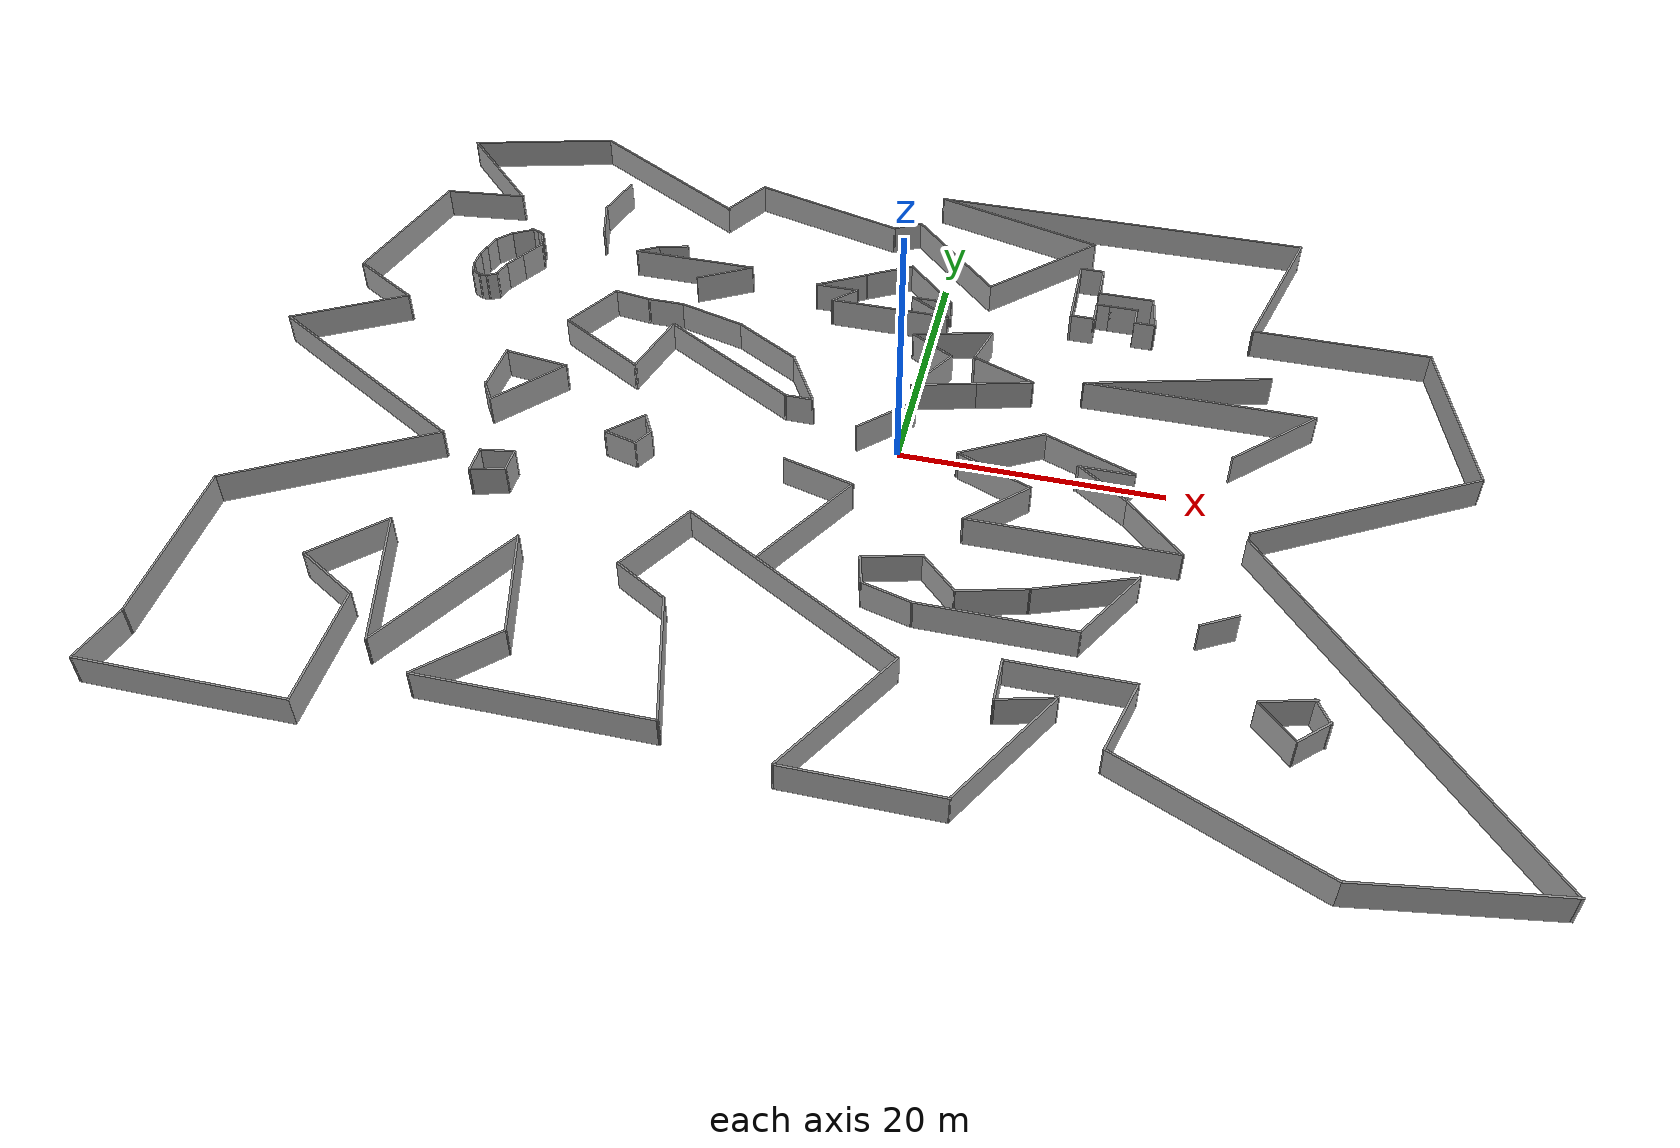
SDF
<?xml version='1.0'?>
<sdf version='1.7'>
  <model name='custommap6'>
    <pose>-1.57023 -1.07201 0 0 -0 0</pose>
    <link name='Wall_0'>
      <collision name='Wall_0_Collision'>
        <geometry>
          <box>
            <size>11.75 0.15 2.5</size>
          </box>
        </geometry>
        <pose>0 0 1.25 0 -0 0</pose>
      </collision>
      <visual name='Wall_0_Visual'>
        <pose>0 0 1.25 0 -0 0</pose>
        <geometry>
          <box>
            <size>11.75 0.15 2.5</size>
          </box>
        </geometry>
        <material>
          <script>
            <uri>file://media/materials/scripts/gazebo.material</uri>
            <name>Gazebo/Grey</name>
          </script>
          <ambient>1 1 1 1</ambient>
        </material>
        <meta>
          <layer>0</layer>
        </meta>
      </visual>
      <pose>-43.8325 16.3365 0 0 -0 -1.8326</pose>
    </link>
    <link name='Wall_1'>
      <collision name='Wall_1_Collision'>
        <geometry>
          <box>
            <size>6.25 0.15 2.5</size>
          </box>
        </geometry>
        <pose>0 0 1.25 0 -0 0</pose>
      </collision>
      <visual name='Wall_1_Visual'>
        <pose>0 0 1.25 0 -0 0</pose>
        <geometry>
          <box>
            <size>6.25 0.15 2.5</size>
          </box>
        </geometry>
        <material>
          <script>
            <uri>file://media/materials/scripts/gazebo.material</uri>
            <name>Gazebo/Grey</name>
          </script>
          <ambient>1 1 1 1</ambient>
        </material>
        <meta>
          <layer>0</layer>
        </meta>
      </visual>
      <pose>-42.6923 9.20912 0 0 -0 -0.523599</pose>
    </link>
    <link name='Wall_10'>
      <collision name='Wall_10_Collision'>
        <geometry>
          <box>
            <size>6.5 0.15 2.5</size>
          </box>
        </geometry>
        <pose>0 0 1.25 0 -0 0</pose>
      </collision>
      <visual name='Wall_10_Visual'>
        <pose>0 0 1.25 0 -0 0</pose>
        <geometry>
          <box>
            <size>6.5 0.15 2.5</size>
          </box>
        </geometry>
        <material>
          <script>
            <uri>file://media/materials/scripts/gazebo.material</uri>
            <name>Gazebo/Grey</name>
          </script>
          <ambient>1 1 1 1</ambient>
        </material>
        <meta>
          <layer>0</layer>
        </meta>
      </visual>
      <pose>-33.5624 -18.2391 0 0 -0 0.785398</pose>
    </link>
    <link name='Wall_100'>
      <collision name='Wall_100_Collision'>
        <geometry>
          <box>
            <size>4.2808 0.15 2.5</size>
          </box>
        </geometry>
        <pose>0 0 1.25 0 -0 0</pose>
      </collision>
      <visual name='Wall_100_Visual'>
        <pose>0 0 1.25 0 -0 0</pose>
        <geometry>
          <box>
            <size>4.2808 0.15 2.5</size>
          </box>
        </geometry>
        <material>
          <script>
            <uri>file://media/materials/scripts/gazebo.material</uri>
            <name>Gazebo/Grey</name>
          </script>
          <ambient>1 1 1 1</ambient>
        </material>
        <meta>
          <layer>0</layer>
        </meta>
      </visual>
      <pose>-29.9794 1.06037 0 0 -0 -1.61612</pose>
    </link>
    <link name='Wall_101'>
      <collision name='Wall_101_Collision'>
        <geometry>
          <box>
            <size>1.95484 0.15 2.5</size>
          </box>
        </geometry>
        <pose>0 0 1.25 0 -0 0</pose>
      </collision>
      <visual name='Wall_101_Visual'>
        <pose>0 0 1.25 0 -0 0</pose>
        <geometry>
          <box>
            <size>1.95484 0.15 2.5</size>
          </box>
        </geometry>
        <material>
          <script>
            <uri>file://media/materials/scripts/gazebo.material</uri>
            <name>Gazebo/Grey</name>
          </script>
          <ambient>1 1 1 1</ambient>
        </material>
        <meta>
          <layer>0</layer>
        </meta>
      </visual>
      <pose>-29.6783 -1.66827 0 0 -0 -0.999139</pose>
    </link>
    <link name='Wall_102'>
      <collision name='Wall_102_Collision'>
        <geometry>
          <box>
            <size>6.66101 0.15 2.5</size>
          </box>
        </geometry>
        <pose>0 0 1.25 0 -0 0</pose>
      </collision>
      <visual name='Wall_102_Visual'>
        <pose>0 0 1.25 0 -0 0</pose>
        <geometry>
          <box>
            <size>6.66101 0.15 2.5</size>
          </box>
        </geometry>
        <material>
          <script>
            <uri>file://media/materials/scripts/gazebo.material</uri>
            <name>Gazebo/Grey</name>
          </script>
          <ambient>1 1 1 1</ambient>
        </material>
        <meta>
          <layer>0</layer>
        </meta>
      </visual>
      <pose>-26.9643 -0.060719 0 0 -0 0.856667</pose>
    </link>
    <link name='Wall_104'>
      <collision name='Wall_104_Collision'>
        <geometry>
          <box>
            <size>5.07582 0.15 2.5</size>
          </box>
        </geometry>
        <pose>0 0 1.25 0 -0 0</pose>
      </collision>
      <visual name='Wall_104_Visual'>
        <pose>0 0 1.25 0 -0 0</pose>
        <geometry>
          <box>
            <size>5.07582 0.15 2.5</size>
          </box>
        </geometry>
        <material>
          <script>
            <uri>file://media/materials/scripts/gazebo.material</uri>
            <name>Gazebo/Grey</name>
          </script>
          <ambient>1 1 1 1</ambient>
        </material>
        <meta>
          <layer>0</layer>
        </meta>
      </visual>
      <pose>-27.2767 2.69877 0 0 -0 -0.121876</pose>
    </link>
    <link name='Wall_107'>
      <collision name='Wall_107_Collision'>
        <geometry>
          <box>
            <size>6.25 0.15 2.5</size>
          </box>
        </geometry>
        <pose>0 0 1.25 0 -0 0</pose>
      </collision>
      <visual name='Wall_107_Visual'>
        <pose>0 0 1.25 0 -0 0</pose>
        <geometry>
          <box>
            <size>6.25 0.15 2.5</size>
          </box>
        </geometry>
        <material>
          <script>
            <uri>file://media/materials/scripts/gazebo.material</uri>
            <name>Gazebo/Grey</name>
          </script>
          <ambient>1 1 1 1</ambient>
        </material>
        <meta>
          <layer>0</layer>
        </meta>
      </visual>
      <pose>3.45301 12.9701 0 0 -0 -2.87979</pose>
    </link>
    <link name='Wall_108'>
      <collision name='Wall_108_Collision'>
        <geometry>
          <box>
            <size>4 0.15 2.5</size>
          </box>
        </geometry>
        <pose>0 0 1.25 0 -0 0</pose>
      </collision>
      <visual name='Wall_108_Visual'>
        <pose>0 0 1.25 0 -0 0</pose>
        <geometry>
          <box>
            <size>4 0.15 2.5</size>
          </box>
        </geometry>
        <material>
          <script>
            <uri>file://media/materials/scripts/gazebo.material</uri>
            <name>Gazebo/Grey</name>
          </script>
          <ambient>1 1 1 1</ambient>
        </material>
        <meta>
          <layer>0</layer>
        </meta>
      </visual>
      <pose>2.17403 11.2182 0 0 -0 -0.523599</pose>
    </link>
    <link name='Wall_109'>
      <collision name='Wall_109_Collision'>
        <geometry>
          <box>
            <size>4.75 0.15 2.5</size>
          </box>
        </geometry>
        <pose>0 0 1.25 0 -0 0</pose>
      </collision>
      <visual name='Wall_109_Visual'>
        <pose>0 0 1.25 0 -0 0</pose>
        <geometry>
          <box>
            <size>4.75 0.15 2.5</size>
          </box>
        </geometry>
        <material>
          <script>
            <uri>file://media/materials/scripts/gazebo.material</uri>
            <name>Gazebo/Grey</name>
          </script>
          <ambient>1 1 1 1</ambient>
        </material>
        <meta>
          <layer>0</layer>
        </meta>
      </visual>
      <pose>2.69113 8.26381 0 0 -0 -2.0944</pose>
    </link>
    <link name='Wall_11'>
      <collision name='Wall_11_Collision'>
        <geometry>
          <box>
            <size>11.25 0.15 2.5</size>
          </box>
        </geometry>
        <pose>0 0 1.25 0 -0 0</pose>
      </collision>
      <visual name='Wall_11_Visual'>
        <pose>0 0 1.25 0 -0 0</pose>
        <geometry>
          <box>
            <size>11.25 0.15 2.5</size>
          </box>
        </geometry>
        <material>
          <script>
            <uri>file://media/materials/scripts/gazebo.material</uri>
            <name>Gazebo/Grey</name>
          </script>
          <ambient>1 1 1 1</ambient>
        </material>
        <meta>
          <layer>0</layer>
        </meta>
      </visual>
      <pose>-29.8809 -21.3549 0 0 -0 -1.309</pose>
    </link>
    <link name='Wall_110'>
      <collision name='Wall_110_Collision'>
        <geometry>
          <box>
            <size>5 0.15 2.5</size>
          </box>
        </geometry>
        <pose>0 0 1.25 0 -0 0</pose>
      </collision>
      <visual name='Wall_110_Visual'>
        <pose>0 0 1.25 0 -0 0</pose>
        <geometry>
          <box>
            <size>5 0.15 2.5</size>
          </box>
        </geometry>
        <material>
          <script>
            <uri>file://media/materials/scripts/gazebo.material</uri>
            <name>Gazebo/Grey</name>
          </script>
          <ambient>1 1 1 1</ambient>
        </material>
        <meta>
          <layer>0</layer>
        </meta>
      </visual>
      <pose>3.8835 6.89959 0 0 -0 0.261799</pose>
    </link>
    <link name='Wall_111'>
      <collision name='Wall_111_Collision'>
        <geometry>
          <box>
            <size>4.5 0.15 2.5</size>
          </box>
        </geometry>
        <pose>0 0 1.25 0 -0 0</pose>
      </collision>
      <visual name='Wall_111_Visual'>
        <pose>0 0 1.25 0 -0 0</pose>
        <geometry>
          <box>
            <size>4.5 0.15 2.5</size>
          </box>
        </geometry>
        <material>
          <script>
            <uri>file://media/materials/scripts/gazebo.material</uri>
            <name>Gazebo/Grey</name>
          </script>
          <ambient>1 1 1 1</ambient>
        </material>
        <meta>
          <layer>0</layer>
        </meta>
      </visual>
      <pose>8.32676 8.09016 0 0 -0 0.261799</pose>
    </link>
    <link name='Wall_112'>
      <collision name='Wall_112_Collision'>
        <geometry>
          <box>
            <size>5.33597 0.15 2.5</size>
          </box>
        </geometry>
        <pose>0 0 1.25 0 -0 0</pose>
      </collision>
      <visual name='Wall_112_Visual'>
        <pose>0 0 1.25 0 -0 0</pose>
        <geometry>
          <box>
            <size>5.33597 0.15 2.5</size>
          </box>
        </geometry>
        <material>
          <script>
            <uri>file://media/materials/scripts/gazebo.material</uri>
            <name>Gazebo/Grey</name>
          </script>
          <ambient>1 1 1 1</ambient>
        </material>
        <meta>
          <layer>0</layer>
        </meta>
      </visual>
      <pose>8.01133 9.5938 0 0 -0 2.77033</pose>
    </link>
    <link name='Wall_113'>
      <collision name='Wall_113_Collision'>
        <geometry>
          <box>
            <size>3.5 0.15 2.5</size>
          </box>
        </geometry>
        <pose>0 0 1.25 0 -0 0</pose>
      </collision>
      <visual name='Wall_113_Visual'>
        <pose>0 0 1.25 0 -0 0</pose>
        <geometry>
          <box>
            <size>3.5 0.15 2.5</size>
          </box>
        </geometry>
        <material>
          <script>
            <uri>file://media/materials/scripts/gazebo.material</uri>
            <name>Gazebo/Grey</name>
          </script>
          <ambient>1 1 1 1</ambient>
        </material>
        <meta>
          <layer>0</layer>
        </meta>
      </visual>
      <pose>6.02853 12.0589 0 0 -0 1.309</pose>
    </link>
    <link name='Wall_115'>
      <collision name='Wall_115_Collision'>
        <geometry>
          <box>
            <size>9.75 0.15 2.5</size>
          </box>
        </geometry>
        <pose>0 0 1.25 0 -0 0</pose>
      </collision>
      <visual name='Wall_115_Visual'>
        <pose>0 0 1.25 0 -0 0</pose>
        <geometry>
          <box>
            <size>9.75 0.15 2.5</size>
          </box>
        </geometry>
        <material>
          <script>
            <uri>file://media/materials/scripts/gazebo.material</uri>
            <name>Gazebo/Grey</name>
          </script>
          <ambient>1 1 1 1</ambient>
        </material>
        <meta>
          <layer>0</layer>
        </meta>
      </visual>
      <pose>-2.89794 -9.40787 0 0 -0 1.0472</pose>
    </link>
    <link name='Wall_116'>
      <collision name='Wall_116_Collision'>
        <geometry>
          <box>
            <size>5.75 0.15 2.5</size>
          </box>
        </geometry>
        <pose>0 0 1.25 0 -0 0</pose>
      </collision>
      <visual name='Wall_116_Visual'>
        <pose>0 0 1.25 0 -0 0</pose>
        <geometry>
          <box>
            <size>5.75 0.15 2.5</size>
          </box>
        </geometry>
        <material>
          <script>
            <uri>file://media/materials/scripts/gazebo.material</uri>
            <name>Gazebo/Grey</name>
          </script>
          <ambient>1 1 1 1</ambient>
        </material>
        <meta>
          <layer>0</layer>
        </meta>
      </visual>
      <pose>-3.20254 -4.52625 0 0 -0 2.87979</pose>
    </link>
    <link name='Wall_118'>
      <collision name='Wall_118_Collision'>
        <geometry>
          <box>
            <size>5.25 0.15 2.5</size>
          </box>
        </geometry>
        <pose>0 0 1.25 0 -0 0</pose>
      </collision>
      <visual name='Wall_118_Visual'>
        <pose>0 0 1.25 0 -0 0</pose>
        <geometry>
          <box>
            <size>5.25 0.15 2.5</size>
          </box>
        </geometry>
        <material>
          <script>
            <uri>file://media/materials/scripts/gazebo.material</uri>
            <name>Gazebo/Grey</name>
          </script>
          <ambient>1 1 1 1</ambient>
        </material>
        <meta>
          <layer>0</layer>
        </meta>
      </visual>
      <pose>0.291453 2.59872 0 0 -0 -2.35619</pose>
    </link>
    <link name='Wall_12'>
      <collision name='Wall_12_Collision'>
        <geometry>
          <box>
            <size>13 0.15 2.5</size>
          </box>
        </geometry>
        <pose>0 0 1.25 0 -0 0</pose>
      </collision>
      <visual name='Wall_12_Visual'>
        <pose>0 0 1.25 0 -0 0</pose>
        <geometry>
          <box>
            <size>13 0.15 2.5</size>
          </box>
        </geometry>
        <material>
          <script>
            <uri>file://media/materials/scripts/gazebo.material</uri>
            <name>Gazebo/Grey</name>
          </script>
          <ambient>1 1 1 1</ambient>
        </material>
        <meta>
          <layer>0</layer>
        </meta>
      </visual>
      <pose>-25.232 -21.1516 0 0 -0 1.0472</pose>
    </link>
    <link name='Wall_120'>
      <collision name='Wall_120_Collision'>
        <geometry>
          <box>
            <size>14.5 0.15 2.5</size>
          </box>
        </geometry>
        <pose>0 0 1.25 0 -0 0</pose>
      </collision>
      <visual name='Wall_120_Visual'>
        <pose>0 0 1.25 0 -0 0</pose>
        <geometry>
          <box>
            <size>14.5 0.15 2.5</size>
          </box>
        </geometry>
        <material>
          <script>
            <uri>file://media/materials/scripts/gazebo.material</uri>
            <name>Gazebo/Grey</name>
          </script>
          <ambient>1 1 1 1</ambient>
        </material>
        <meta>
          <layer>0</layer>
        </meta>
      </visual>
      <pose>21.1782 11.341 0 0 -0 -2.87979</pose>
    </link>
    <link name='Wall_121'>
      <collision name='Wall_121_Collision'>
        <geometry>
          <box>
            <size>17.5 0.15 2.5</size>
          </box>
        </geometry>
        <pose>0 0 1.25 0 -0 0</pose>
      </collision>
      <visual name='Wall_121_Visual'>
        <pose>0 0 1.25 0 -0 0</pose>
        <geometry>
          <box>
            <size>17.5 0.15 2.5</size>
          </box>
        </geometry>
        <material>
          <script>
            <uri>file://media/materials/scripts/gazebo.material</uri>
            <name>Gazebo/Grey</name>
          </script>
          <ambient>1 1 1 1</ambient>
        </material>
        <meta>
          <layer>0</layer>
        </meta>
      </visual>
      <pose>22.9227 9.48395 0 0 -0 0</pose>
    </link>
    <link name='Wall_122'>
      <collision name='Wall_122_Collision'>
        <geometry>
          <box>
            <size>8.25 0.15 2.5</size>
          </box>
        </geometry>
        <pose>0 0 1.25 0 -0 0</pose>
      </collision>
      <visual name='Wall_122_Visual'>
        <pose>0 0 1.25 0 -0 0</pose>
        <geometry>
          <box>
            <size>8.25 0.15 2.5</size>
          </box>
        </geometry>
        <material>
          <script>
            <uri>file://media/materials/scripts/gazebo.material</uri>
            <name>Gazebo/Grey</name>
          </script>
          <ambient>1 1 1 1</ambient>
        </material>
        <meta>
          <layer>0</layer>
        </meta>
      </visual>
      <pose>28.7339 6.62017 0 0 -0 -2.35619</pose>
    </link>
    <link name='Wall_124'>
      <collision name='Wall_124_Collision'>
        <geometry>
          <box>
            <size>4.25 0.15 2.5</size>
          </box>
        </geometry>
        <pose>0 0 1.25 0 -0 0</pose>
      </collision>
      <visual name='Wall_124_Visual'>
        <pose>0 0 1.25 0 -0 0</pose>
        <geometry>
          <box>
            <size>4.25 0.15 2.5</size>
          </box>
        </geometry>
        <material>
          <script>
            <uri>file://media/materials/scripts/gazebo.material</uri>
            <name>Gazebo/Grey</name>
          </script>
          <ambient>1 1 1 1</ambient>
        </material>
        <meta>
          <layer>0</layer>
        </meta>
      </visual>
      <pose>-6.60542 17.6004 0 0 -0 -2.61799</pose>
    </link>
    <link name='Wall_125'>
      <collision name='Wall_125_Collision'>
        <geometry>
          <box>
            <size>3.5 0.15 2.5</size>
          </box>
        </geometry>
        <pose>0 0 1.25 0 -0 0</pose>
      </collision>
      <visual name='Wall_125_Visual'>
        <pose>0 0 1.25 0 -0 0</pose>
        <geometry>
          <box>
            <size>3.5 0.15 2.5</size>
          </box>
        </geometry>
        <material>
          <script>
            <uri>file://media/materials/scripts/gazebo.material</uri>
            <name>Gazebo/Grey</name>
          </script>
          <ambient>1 1 1 1</ambient>
        </material>
        <meta>
          <layer>0</layer>
        </meta>
      </visual>
      <pose>-6.70577 16.5754 0 0 -0 0</pose>
    </link>
    <link name='Wall_126'>
      <collision name='Wall_126_Collision'>
        <geometry>
          <box>
            <size>2.5 0.15 2.5</size>
          </box>
        </geometry>
        <pose>0 0 1.25 0 -0 0</pose>
      </collision>
      <visual name='Wall_126_Visual'>
        <pose>0 0 1.25 0 -0 0</pose>
        <geometry>
          <box>
            <size>2.5 0.15 2.5</size>
          </box>
        </geometry>
        <material>
          <script>
            <uri>file://media/materials/scripts/gazebo.material</uri>
            <name>Gazebo/Grey</name>
          </script>
          <ambient>1 1 1 1</ambient>
        </material>
        <meta>
          <layer>0</layer>
        </meta>
      </visual>
      <pose>-5.86162 15.7446 0 0 -0 -2.35619</pose>
    </link>
    <link name='Wall_127'>
      <collision name='Wall_127_Collision'>
        <geometry>
          <box>
            <size>9.5 0.15 2.5</size>
          </box>
        </geometry>
        <pose>0 0 1.25 0 -0 0</pose>
      </collision>
      <visual name='Wall_127_Visual'>
        <pose>0 0 1.25 0 -0 0</pose>
        <geometry>
          <box>
            <size>9.5 0.15 2.5</size>
          </box>
        </geometry>
        <material>
          <script>
            <uri>file://media/materials/scripts/gazebo.material</uri>
            <name>Gazebo/Grey</name>
          </script>
          <ambient>1 1 1 1</ambient>
        </material>
        <meta>
          <layer>0</layer>
        </meta>
      </visual>
      <pose>-2.01747 14.9137 0 0 -0 0</pose>
    </link>
    <link name='Wall_128'>
      <collision name='Wall_128_Collision'>
        <geometry>
          <box>
            <size>3.75 0.15 2.5</size>
          </box>
        </geometry>
        <pose>0 0 1.25 0 -0 0</pose>
      </collision>
      <visual name='Wall_128_Visual'>
        <pose>0 0 1.25 0 -0 0</pose>
        <geometry>
          <box>
            <size>3.75 0.15 2.5</size>
          </box>
        </geometry>
        <material>
          <script>
            <uri>file://media/materials/scripts/gazebo.material</uri>
            <name>Gazebo/Grey</name>
          </script>
          <ambient>1 1 1 1</ambient>
        </material>
        <meta>
          <layer>0</layer>
        </meta>
      </visual>
      <pose>1.09868 15.8137 0 0 -0 2.61799</pose>
    </link>
    <link name='Wall_129'>
      <collision name='Wall_129_Collision'>
        <geometry>
          <box>
            <size>3.25 0.15 2.5</size>
          </box>
        </geometry>
        <pose>0 0 1.25 0 -0 0</pose>
      </collision>
      <visual name='Wall_129_Visual'>
        <pose>0 0 1.25 0 -0 0</pose>
        <geometry>
          <box>
            <size>3.25 0.15 2.5</size>
          </box>
        </geometry>
        <material>
          <script>
            <uri>file://media/materials/scripts/gazebo.material</uri>
            <name>Gazebo/Grey</name>
          </script>
          <ambient>1 1 1 1</ambient>
        </material>
        <meta>
          <layer>0</layer>
        </meta>
      </visual>
      <pose>1.08984 16.7137 0 0 -0 0</pose>
    </link>
    <link name='Wall_13'>
      <collision name='Wall_13_Collision'>
        <geometry>
          <box>
            <size>8.75 0.15 2.5</size>
          </box>
        </geometry>
        <pose>0 0 1.25 0 -0 0</pose>
      </collision>
      <visual name='Wall_13_Visual'>
        <pose>0 0 1.25 0 -0 0</pose>
        <geometry>
          <box>
            <size>8.75 0.15 2.5</size>
          </box>
        </geometry>
        <material>
          <script>
            <uri>file://media/materials/scripts/gazebo.material</uri>
            <name>Gazebo/Grey</name>
          </script>
          <ambient>1 1 1 1</ambient>
        </material>
        <meta>
          <layer>0</layer>
        </meta>
      </visual>
      <pose>-20.9066 -19.7408 0 0 -0 -1.309</pose>
    </link>
    <link name='Wall_130'>
      <collision name='Wall_130_Collision'>
        <geometry>
          <box>
            <size>5.75 0.15 2.5</size>
          </box>
        </geometry>
        <pose>0 0 1.25 0 -0 0</pose>
      </collision>
      <visual name='Wall_130_Visual'>
        <pose>0 0 1.25 0 -0 0</pose>
        <geometry>
          <box>
            <size>5.75 0.15 2.5</size>
          </box>
        </geometry>
        <material>
          <script>
            <uri>file://media/materials/scripts/gazebo.material</uri>
            <name>Gazebo/Grey</name>
          </script>
          <ambient>1 1 1 1</ambient>
        </material>
        <meta>
          <layer>0</layer>
        </meta>
      </visual>
      <pose>0.65994 18.6936 0 0 -0 2.35619</pose>
    </link>
    <link name='Wall_131'>
      <collision name='Wall_131_Collision'>
        <geometry>
          <box>
            <size>4 0.15 2.5</size>
          </box>
        </geometry>
        <pose>0 0 1.25 0 -0 0</pose>
      </collision>
      <visual name='Wall_131_Visual'>
        <pose>0 0 1.25 0 -0 0</pose>
        <geometry>
          <box>
            <size>4 0.15 2.5</size>
          </box>
        </geometry>
        <material>
          <script>
            <uri>file://media/materials/scripts/gazebo.material</uri>
            <name>Gazebo/Grey</name>
          </script>
          <ambient>1 1 1 1</ambient>
        </material>
        <meta>
          <layer>0</layer>
        </meta>
      </visual>
      <pose>-2.98706 19.711 0 0 -0 -2.61799</pose>
    </link>
    <link name='Wall_133'>
      <collision name='Wall_133_Collision'>
        <geometry>
          <box>
            <size>4.5 0.15 2.5</size>
          </box>
        </geometry>
        <pose>0 0 1.25 0 -0 0</pose>
      </collision>
      <visual name='Wall_133_Visual'>
        <pose>0 0 1.25 0 -0 0</pose>
        <geometry>
          <box>
            <size>4.5 0.15 2.5</size>
          </box>
        </geometry>
        <material>
          <script>
            <uri>file://media/materials/scripts/gazebo.material</uri>
            <name>Gazebo/Grey</name>
          </script>
          <ambient>1 1 1 1</ambient>
        </material>
        <meta>
          <layer>0</layer>
        </meta>
      </visual>
      <pose>16.2018 20.6841 0 0 -0 3.14159</pose>
    </link>
    <link name='Wall_134'>
      <collision name='Wall_134_Collision'>
        <geometry>
          <box>
            <size>3 0.15 2.5</size>
          </box>
        </geometry>
        <pose>0 0 1.25 0 -0 0</pose>
      </collision>
      <visual name='Wall_134_Visual'>
        <pose>0 0 1.25 0 -0 0</pose>
        <geometry>
          <box>
            <size>3 0.15 2.5</size>
          </box>
        </geometry>
        <material>
          <script>
            <uri>file://media/materials/scripts/gazebo.material</uri>
            <name>Gazebo/Grey</name>
          </script>
          <ambient>1 1 1 1</ambient>
        </material>
        <meta>
          <layer>0</layer>
        </meta>
      </visual>
      <pose>14.0268 22.1091 0 0 -0 1.5708</pose>
    </link>
    <link name='Wall_135'>
      <collision name='Wall_135_Collision'>
        <geometry>
          <box>
            <size>2 0.15 2.5</size>
          </box>
        </geometry>
        <pose>0 0 1.25 0 -0 0</pose>
      </collision>
      <visual name='Wall_135_Visual'>
        <pose>0 0 1.25 0 -0 0</pose>
        <geometry>
          <box>
            <size>2 0.15 2.5</size>
          </box>
        </geometry>
        <material>
          <script>
            <uri>file://media/materials/scripts/gazebo.material</uri>
            <name>Gazebo/Grey</name>
          </script>
          <ambient>1 1 1 1</ambient>
        </material>
        <meta>
          <layer>0</layer>
        </meta>
      </visual>
      <pose>13.1018 23.5341 0 0 -0 3.14159</pose>
    </link>
    <link name='Wall_136'>
      <collision name='Wall_136_Collision'>
        <geometry>
          <box>
            <size>3.25 0.15 2.5</size>
          </box>
        </geometry>
        <pose>0 0 1.25 0 -0 0</pose>
      </collision>
      <visual name='Wall_136_Visual'>
        <pose>0 0 1.25 0 -0 0</pose>
        <geometry>
          <box>
            <size>3.25 0.15 2.5</size>
          </box>
        </geometry>
        <material>
          <script>
            <uri>file://media/materials/scripts/gazebo.material</uri>
            <name>Gazebo/Grey</name>
          </script>
          <ambient>1 1 1 1</ambient>
        </material>
        <meta>
          <layer>0</layer>
        </meta>
      </visual>
      <pose>12.1768 21.9841 0 0 -0 -1.5708</pose>
    </link>
    <link name='Wall_137'>
      <collision name='Wall_137_Collision'>
        <geometry>
          <box>
            <size>3.25 0.15 2.5</size>
          </box>
        </geometry>
        <pose>0 0 1.25 0 -0 0</pose>
      </collision>
      <visual name='Wall_137_Visual'>
        <pose>0 0 1.25 0 -0 0</pose>
        <geometry>
          <box>
            <size>3.25 0.15 2.5</size>
          </box>
        </geometry>
        <material>
          <script>
            <uri>file://media/materials/scripts/gazebo.material</uri>
            <name>Gazebo/Grey</name>
          </script>
          <ambient>1 1 1 1</ambient>
        </material>
        <meta>
          <layer>0</layer>
        </meta>
      </visual>
      <pose>12.1768 18.8841 0 0 -0 -1.5708</pose>
    </link>
    <link name='Wall_138'>
      <collision name='Wall_138_Collision'>
        <geometry>
          <box>
            <size>2 0.15 2.5</size>
          </box>
        </geometry>
        <pose>0 0 1.25 0 -0 0</pose>
      </collision>
      <visual name='Wall_138_Visual'>
        <pose>0 0 1.25 0 -0 0</pose>
        <geometry>
          <box>
            <size>2 0.15 2.5</size>
          </box>
        </geometry>
        <material>
          <script>
            <uri>file://media/materials/scripts/gazebo.material</uri>
            <name>Gazebo/Grey</name>
          </script>
          <ambient>1 1 1 1</ambient>
        </material>
        <meta>
          <layer>0</layer>
        </meta>
      </visual>
      <pose>13.1018 17.3341 0 0 -0 0</pose>
    </link>
    <link name='Wall_139'>
      <collision name='Wall_139_Collision'>
        <geometry>
          <box>
            <size>2 0.15 2.5</size>
          </box>
        </geometry>
        <pose>0 0 1.25 0 -0 0</pose>
      </collision>
      <visual name='Wall_139_Visual'>
        <pose>0 0 1.25 0 -0 0</pose>
        <geometry>
          <box>
            <size>2 0.15 2.5</size>
          </box>
        </geometry>
        <material>
          <script>
            <uri>file://media/materials/scripts/gazebo.material</uri>
            <name>Gazebo/Grey</name>
          </script>
          <ambient>1 1 1 1</ambient>
        </material>
        <meta>
          <layer>0</layer>
        </meta>
      </visual>
      <pose>14.0268 18.2591 0 0 -0 1.5708</pose>
    </link>
    <link name='Wall_14'>
      <collision name='Wall_14_Collision'>
        <geometry>
          <box>
            <size>7 0.15 2.5</size>
          </box>
        </geometry>
        <pose>0 0 1.25 0 -0 0</pose>
      </collision>
      <visual name='Wall_14_Visual'>
        <pose>0 0 1.25 0 -0 0</pose>
        <geometry>
          <box>
            <size>7 0.15 2.5</size>
          </box>
        </geometry>
        <material>
          <script>
            <uri>file://media/materials/scripts/gazebo.material</uri>
            <name>Gazebo/Grey</name>
          </script>
          <ambient>1 1 1 1</ambient>
        </material>
        <meta>
          <layer>0</layer>
        </meta>
      </visual>
      <pose>-22.2155 -26.3162 0 0 -0 -2.35619</pose>
    </link>
    <link name='Wall_140'>
      <collision name='Wall_140_Collision'>
        <geometry>
          <box>
            <size>1.25 0.15 2.5</size>
          </box>
        </geometry>
        <pose>0 0 1.25 0 -0 0</pose>
      </collision>
      <visual name='Wall_140_Visual'>
        <pose>0 0 1.25 0 -0 0</pose>
        <geometry>
          <box>
            <size>1.25 0.15 2.5</size>
          </box>
        </geometry>
        <material>
          <script>
            <uri>file://media/materials/scripts/gazebo.material</uri>
            <name>Gazebo/Grey</name>
          </script>
          <ambient>1 1 1 1</ambient>
        </material>
        <meta>
          <layer>0</layer>
        </meta>
      </visual>
      <pose>14.5768 19.1841 0 0 -0 0</pose>
    </link>
    <link name='Wall_141'>
      <collision name='Wall_141_Collision'>
        <geometry>
          <box>
            <size>2.25 0.15 2.5</size>
          </box>
        </geometry>
        <pose>0 0 1.25 0 -0 0</pose>
      </collision>
      <visual name='Wall_141_Visual'>
        <pose>0 0 1.25 0 -0 0</pose>
        <geometry>
          <box>
            <size>2.25 0.15 2.5</size>
          </box>
        </geometry>
        <material>
          <script>
            <uri>file://media/materials/scripts/gazebo.material</uri>
            <name>Gazebo/Grey</name>
          </script>
          <ambient>1 1 1 1</ambient>
        </material>
        <meta>
          <layer>0</layer>
        </meta>
      </visual>
      <pose>16.1768 19.1841 0 0 -0 0</pose>
    </link>
    <link name='Wall_142'>
      <collision name='Wall_142_Collision'>
        <geometry>
          <box>
            <size>1.75 0.15 2.5</size>
          </box>
        </geometry>
        <pose>0 0 1.25 0 -0 0</pose>
      </collision>
      <visual name='Wall_142_Visual'>
        <pose>0 0 1.25 0 -0 0</pose>
        <geometry>
          <box>
            <size>1.75 0.15 2.5</size>
          </box>
        </geometry>
        <material>
          <script>
            <uri>file://media/materials/scripts/gazebo.material</uri>
            <name>Gazebo/Grey</name>
          </script>
          <ambient>1 1 1 1</ambient>
        </material>
        <meta>
          <layer>0</layer>
        </meta>
      </visual>
      <pose>17.2268 18.3841 0 0 -0 -1.5708</pose>
    </link>
    <link name='Wall_143'>
      <collision name='Wall_143_Collision'>
        <geometry>
          <box>
            <size>1.75 0.15 2.5</size>
          </box>
        </geometry>
        <pose>0 0 1.25 0 -0 0</pose>
      </collision>
      <visual name='Wall_143_Visual'>
        <pose>0 0 1.25 0 -0 0</pose>
        <geometry>
          <box>
            <size>1.75 0.15 2.5</size>
          </box>
        </geometry>
        <material>
          <script>
            <uri>file://media/materials/scripts/gazebo.material</uri>
            <name>Gazebo/Grey</name>
          </script>
          <ambient>1 1 1 1</ambient>
        </material>
        <meta>
          <layer>0</layer>
        </meta>
      </visual>
      <pose>18.0268 17.5841 0 0 -0 0</pose>
    </link>
    <link name='Wall_144'>
      <collision name='Wall_144_Collision'>
        <geometry>
          <box>
            <size>3.28249 0.15 2.5</size>
          </box>
        </geometry>
        <pose>0 0 1.25 0 -0 0</pose>
      </collision>
      <visual name='Wall_144_Visual'>
        <pose>0 0 1.25 0 -0 0</pose>
        <geometry>
          <box>
            <size>3.28249 0.15 2.5</size>
          </box>
        </geometry>
        <material>
          <script>
            <uri>file://media/materials/scripts/gazebo.material</uri>
            <name>Gazebo/Grey</name>
          </script>
          <ambient>1 1 1 1</ambient>
        </material>
        <meta>
          <layer>0</layer>
        </meta>
      </visual>
      <pose>18.6018 19.1341 0 0 -0 1.71495</pose>
    </link>
    <link name='Wall_146'>
      <collision name='Wall_146_Collision'>
        <geometry>
          <box>
            <size>5.25 0.15 2.5</size>
          </box>
        </geometry>
        <pose>0 0 1.25 0 -0 0</pose>
      </collision>
      <visual name='Wall_146_Visual'>
        <pose>0 0 1.25 0 -0 0</pose>
        <geometry>
          <box>
            <size>5.25 0.15 2.5</size>
          </box>
        </geometry>
        <material>
          <script>
            <uri>file://media/materials/scripts/gazebo.material</uri>
            <name>Gazebo/Grey</name>
          </script>
          <ambient>1 1 1 1</ambient>
        </material>
        <meta>
          <layer>0</layer>
        </meta>
      </visual>
      <pose>10.9542 -13.0083 0 0 -0 -2.87979</pose>
    </link>
    <link name='Wall_147'>
      <collision name='Wall_147_Collision'>
        <geometry>
          <box>
            <size>4 0.15 2.5</size>
          </box>
        </geometry>
        <pose>0 0 1.25 0 -0 0</pose>
      </collision>
      <visual name='Wall_147_Visual'>
        <pose>0 0 1.25 0 -0 0</pose>
        <geometry>
          <box>
            <size>4 0.15 2.5</size>
          </box>
        </geometry>
        <material>
          <script>
            <uri>file://media/materials/scripts/gazebo.material</uri>
            <name>Gazebo/Grey</name>
          </script>
          <ambient>1 1 1 1</ambient>
        </material>
        <meta>
          <layer>0</layer>
        </meta>
      </visual>
      <pose>7.12989 -12.3071 0 0 -0 2.35619</pose>
    </link>
    <link name='Wall_148'>
      <collision name='Wall_148_Collision'>
        <geometry>
          <box>
            <size>4.5 0.15 2.5</size>
          </box>
        </geometry>
        <pose>0 0 1.25 0 -0 0</pose>
      </collision>
      <visual name='Wall_148_Visual'>
        <pose>0 0 1.25 0 -0 0</pose>
        <geometry>
          <box>
            <size>4.5 0.15 2.5</size>
          </box>
        </geometry>
        <material>
          <script>
            <uri>file://media/materials/scripts/gazebo.material</uri>
            <name>Gazebo/Grey</name>
          </script>
          <ambient>1 1 1 1</ambient>
        </material>
        <meta>
          <layer>0</layer>
        </meta>
      </visual>
      <pose>3.66783 -11.5088 0 0 -0 -2.87979</pose>
    </link>
    <link name='Wall_149'>
      <collision name='Wall_149_Collision'>
        <geometry>
          <box>
            <size>2.5 0.15 2.5</size>
          </box>
        </geometry>
        <pose>0 0 1.25 0 -0 0</pose>
      </collision>
      <visual name='Wall_149_Visual'>
        <pose>0 0 1.25 0 -0 0</pose>
        <geometry>
          <box>
            <size>2.5 0.15 2.5</size>
          </box>
        </geometry>
        <material>
          <script>
            <uri>file://media/materials/scripts/gazebo.material</uri>
            <name>Gazebo/Grey</name>
          </script>
          <ambient>1 1 1 1</ambient>
        </material>
        <meta>
          <layer>0</layer>
        </meta>
      </visual>
      <pose>1.87105 -13.2067 0 0 -0 -1.309</pose>
    </link>
    <link name='Wall_15'>
      <collision name='Wall_15_Collision'>
        <geometry>
          <box>
            <size>17 0.15 2.5</size>
          </box>
        </geometry>
        <pose>0 0 1.25 0 -0 0</pose>
      </collision>
      <visual name='Wall_15_Visual'>
        <pose>0 0 1.25 0 -0 0</pose>
        <geometry>
          <box>
            <size>17 0.15 2.5</size>
          </box>
        </geometry>
        <material>
          <script>
            <uri>file://media/materials/scripts/gazebo.material</uri>
            <name>Gazebo/Grey</name>
          </script>
          <ambient>1 1 1 1</ambient>
        </material>
        <meta>
          <layer>0</layer>
        </meta>
      </visual>
      <pose>-16.2123 -28.738 0 0 -0 0</pose>
    </link>
    <link name='Wall_150'>
      <collision name='Wall_150_Collision'>
        <geometry>
          <box>
            <size>4 0.15 2.5</size>
          </box>
        </geometry>
        <pose>0 0 1.25 0 -0 0</pose>
      </collision>
      <visual name='Wall_150_Visual'>
        <pose>0 0 1.25 0 -0 0</pose>
        <geometry>
          <box>
            <size>4 0.15 2.5</size>
          </box>
        </geometry>
        <material>
          <script>
            <uri>file://media/materials/scripts/gazebo.material</uri>
            <name>Gazebo/Grey</name>
          </script>
          <ambient>1 1 1 1</ambient>
        </material>
        <meta>
          <layer>0</layer>
        </meta>
      </visual>
      <pose>4.03457 -14.8399 0 0 -0 -0.261799</pose>
    </link>
    <link name='Wall_151'>
      <collision name='Wall_151_Collision'>
        <geometry>
          <box>
            <size>11.5 0.15 2.5</size>
          </box>
        </geometry>
        <pose>0 0 1.25 0 -0 0</pose>
      </collision>
      <visual name='Wall_151_Visual'>
        <pose>0 0 1.25 0 -0 0</pose>
        <geometry>
          <box>
            <size>11.5 0.15 2.5</size>
          </box>
        </geometry>
        <material>
          <script>
            <uri>file://media/materials/scripts/gazebo.material</uri>
            <name>Gazebo/Grey</name>
          </script>
          <ambient>1 1 1 1</ambient>
        </material>
        <meta>
          <layer>0</layer>
        </meta>
      </visual>
      <pose>11.569 -15.3382 0 0 -0 0</pose>
    </link>
    <link name='Wall_152'>
      <collision name='Wall_152_Collision'>
        <geometry>
          <box>
            <size>6.75 0.15 2.5</size>
          </box>
        </geometry>
        <pose>0 0 1.25 0 -0 0</pose>
      </collision>
      <visual name='Wall_152_Visual'>
        <pose>0 0 1.25 0 -0 0</pose>
        <geometry>
          <box>
            <size>6.75 0.15 2.5</size>
          </box>
        </geometry>
        <material>
          <script>
            <uri>file://media/materials/scripts/gazebo.material</uri>
            <name>Gazebo/Grey</name>
          </script>
          <ambient>1 1 1 1</ambient>
        </material>
        <meta>
          <layer>0</layer>
        </meta>
      </visual>
      <pose>18.894 -12.4803 0 0 -0 1.0472</pose>
    </link>
    <link name='Wall_153'>
      <collision name='Wall_153_Collision'>
        <geometry>
          <box>
            <size>7.78021 0.15 2.5</size>
          </box>
        </geometry>
        <pose>0 0 1.25 0 -0 0</pose>
      </collision>
      <visual name='Wall_153_Visual'>
        <pose>0 0 1.25 0 -0 0</pose>
        <geometry>
          <box>
            <size>7.78021 0.15 2.5</size>
          </box>
        </geometry>
        <material>
          <script>
            <uri>file://media/materials/scripts/gazebo.material</uri>
            <name>Gazebo/Grey</name>
          </script>
          <ambient>1 1 1 1</ambient>
        </material>
        <meta>
          <layer>0</layer>
        </meta>
      </visual>
      <pose>16.9806 -10.9853 0 0 -0 -2.77627</pose>
    </link>
    <link name='Wall_155'>
      <collision name='Wall_155_Collision'>
        <geometry>
          <box>
            <size>4 0.15 2.5</size>
          </box>
        </geometry>
        <pose>0 0 1.25 0 -0 0</pose>
      </collision>
      <visual name='Wall_155_Visual'>
        <pose>0 0 1.25 0 -0 0</pose>
        <geometry>
          <box>
            <size>4 0.15 2.5</size>
          </box>
        </geometry>
        <material>
          <script>
            <uri>file://media/materials/scripts/gazebo.material</uri>
            <name>Gazebo/Grey</name>
          </script>
          <ambient>1 1 1 1</ambient>
        </material>
        <meta>
          <layer>0</layer>
        </meta>
      </visual>
      <pose>30.8646 -18.0666 0 0 -0 -2.87979</pose>
    </link>
    <link name='Wall_156'>
      <collision name='Wall_156_Collision'>
        <geometry>
          <box>
            <size>3.76094 0.15 2.5</size>
          </box>
        </geometry>
        <pose>0 0 1.25 0 -0 0</pose>
      </collision>
      <visual name='Wall_156_Visual'>
        <pose>0 0 1.25 0 -0 0</pose>
        <geometry>
          <box>
            <size>3.76094 0.15 2.5</size>
          </box>
        </geometry>
        <material>
          <script>
            <uri>file://media/materials/scripts/gazebo.material</uri>
            <name>Gazebo/Grey</name>
          </script>
          <ambient>1 1 1 1</ambient>
        </material>
        <meta>
          <layer>0</layer>
        </meta>
      </visual>
      <pose>30.2818 -19.9491 0 0 -0 -0.785398</pose>
    </link>
    <link name='Wall_157'>
      <collision name='Wall_157_Collision'>
        <geometry>
          <box>
            <size>2.99248 0.15 2.5</size>
          </box>
        </geometry>
        <pose>0 0 1.25 0 -0 0</pose>
      </collision>
      <visual name='Wall_157_Visual'>
        <pose>0 0 1.25 0 -0 0</pose>
        <geometry>
          <box>
            <size>2.99248 0.15 2.5</size>
          </box>
        </geometry>
        <material>
          <script>
            <uri>file://media/materials/scripts/gazebo.material</uri>
            <name>Gazebo/Grey</name>
          </script>
          <ambient>1 1 1 1</ambient>
        </material>
        <meta>
          <layer>0</layer>
        </meta>
      </visual>
      <pose>32.578 -20.2355 0 0 -0 0.770832</pose>
    </link>
    <link name='Wall_158'>
      <collision name='Wall_158_Collision'>
        <geometry>
          <box>
            <size>2.25 0.15 2.5</size>
          </box>
        </geometry>
        <pose>0 0 1.25 0 -0 0</pose>
      </collision>
      <visual name='Wall_158_Visual'>
        <pose>0 0 1.25 0 -0 0</pose>
        <geometry>
          <box>
            <size>2.25 0.15 2.5</size>
          </box>
        </geometry>
        <material>
          <script>
            <uri>file://media/materials/scripts/gazebo.material</uri>
            <name>Gazebo/Grey</name>
          </script>
          <ambient>1 1 1 1</ambient>
        </material>
        <meta>
          <layer>0</layer>
        </meta>
      </visual>
      <pose>33.0725 -18.4436 0 0 -0 2.0944</pose>
    </link>
    <link name='Wall_16'>
      <collision name='Wall_16_Collision'>
        <geometry>
          <box>
            <size>10.5 0.15 2.5</size>
          </box>
        </geometry>
        <pose>0 0 1.25 0 -0 0</pose>
      </collision>
      <visual name='Wall_16_Visual'>
        <pose>0 0 1.25 0 -0 0</pose>
        <geometry>
          <box>
            <size>10.5 0.15 2.5</size>
          </box>
        </geometry>
        <material>
          <script>
            <uri>file://media/materials/scripts/gazebo.material</uri>
            <name>Gazebo/Grey</name>
          </script>
          <ambient>1 1 1 1</ambient>
        </material>
        <meta>
          <layer>0</layer>
        </meta>
      </visual>
      <pose>-9.12671 -23.7393 0 0 -0 1.8326</pose>
    </link>
    <link name='Wall_160'>
      <collision name='Wall_160_Collision'>
        <geometry>
          <box>
            <size>3 0.15 2.5</size>
          </box>
        </geometry>
        <pose>0 0 1.25 0 -0 0</pose>
      </collision>
      <visual name='Wall_160_Visual'>
        <pose>0 0 1.25 0 -0 0</pose>
        <geometry>
          <box>
            <size>3 0.15 2.5</size>
          </box>
        </geometry>
        <material>
          <script>
            <uri>file://media/materials/scripts/gazebo.material</uri>
            <name>Gazebo/Grey</name>
          </script>
          <ambient>1 1 1 1</ambient>
        </material>
        <meta>
          <layer>0</layer>
        </meta>
      </visual>
      <pose>26.1093 -12.2546 0 0 -0 -2.61799</pose>
    </link>
    <link name='Wall_162'>
      <collision name='Wall_162_Collision'>
        <geometry>
          <box>
            <size>4 0.15 2.5</size>
          </box>
        </geometry>
        <pose>0 0 1.25 0 -0 0</pose>
      </collision>
      <visual name='Wall_162_Visual'>
        <pose>0 0 1.25 0 -0 0</pose>
        <geometry>
          <box>
            <size>4 0.15 2.5</size>
          </box>
        </geometry>
        <material>
          <script>
            <uri>file://media/materials/scripts/gazebo.material</uri>
            <name>Gazebo/Grey</name>
          </script>
          <ambient>1 1 1 1</ambient>
        </material>
        <meta>
          <layer>0</layer>
        </meta>
      </visual>
      <pose>-27.8334 24.5468 0 0 -0 -1.8326</pose>
    </link>
    <link name='Wall_163'>
      <collision name='Wall_163_Collision'>
        <geometry>
          <box>
            <size>3.5 0.15 2.5</size>
          </box>
        </geometry>
        <pose>0 0 1.25 0 -0 0</pose>
      </collision>
      <visual name='Wall_163_Visual'>
        <pose>0 0 1.25 0 -0 0</pose>
        <geometry>
          <box>
            <size>3.5 0.15 2.5</size>
          </box>
        </geometry>
        <material>
          <script>
            <uri>file://media/materials/scripts/gazebo.material</uri>
            <name>Gazebo/Grey</name>
          </script>
          <ambient>1 1 1 1</ambient>
        </material>
        <meta>
          <layer>0</layer>
        </meta>
      </visual>
      <pose>-27.8981 21.0695 0 0 -0 -1.309</pose>
    </link>
    <link name='Wall_17'>
      <collision name='Wall_17_Collision'>
        <geometry>
          <box>
            <size>4.75 0.15 2.5</size>
          </box>
        </geometry>
        <pose>0 0 1.25 0 -0 0</pose>
      </collision>
      <visual name='Wall_17_Visual'>
        <pose>0 0 1.25 0 -0 0</pose>
        <geometry>
          <box>
            <size>4.75 0.15 2.5</size>
          </box>
        </geometry>
        <material>
          <script>
            <uri>file://media/materials/scripts/gazebo.material</uri>
            <name>Gazebo/Grey</name>
          </script>
          <ambient>1 1 1 1</ambient>
        </material>
        <meta>
          <layer>0</layer>
        </meta>
      </visual>
      <pose>-12.458 -17.5907 0 0 -0 2.61799</pose>
    </link>
    <link name='Wall_18'>
      <collision name='Wall_18_Collision'>
        <geometry>
          <box>
            <size>7 0.15 2.5</size>
          </box>
        </geometry>
        <pose>0 0 1.25 0 -0 0</pose>
      </collision>
      <visual name='Wall_18_Visual'>
        <pose>0 0 1.25 0 -0 0</pose>
        <geometry>
          <box>
            <size>7 0.15 2.5</size>
          </box>
        </geometry>
        <material>
          <script>
            <uri>file://media/materials/scripts/gazebo.material</uri>
            <name>Gazebo/Grey</name>
          </script>
          <ambient>1 1 1 1</ambient>
        </material>
        <meta>
          <layer>0</layer>
        </meta>
      </visual>
      <pose>-12.7373 -13.4745 0 0 -0 1.0472</pose>
    </link>
    <link name='Wall_19'>
      <collision name='Wall_19_Collision'>
        <geometry>
          <box>
            <size>19.75 0.15 2.5</size>
          </box>
        </geometry>
        <pose>0 0 1.25 0 -0 0</pose>
      </collision>
      <visual name='Wall_19_Visual'>
        <pose>0 0 1.25 0 -0 0</pose>
        <geometry>
          <box>
            <size>19.75 0.15 2.5</size>
          </box>
        </geometry>
        <material>
          <script>
            <uri>file://media/materials/scripts/gazebo.material</uri>
            <name>Gazebo/Grey</name>
          </script>
          <ambient>1 1 1 1</ambient>
        </material>
        <meta>
          <layer>0</layer>
        </meta>
      </visual>
      <pose>-2.53776 -15.4084 0 0 -0 -0.523599</pose>
    </link>
    <link name='Wall_2'>
      <collision name='Wall_2_Collision'>
        <geometry>
          <box>
            <size>9.5 0.15 2.5</size>
          </box>
        </geometry>
        <pose>0 0 1.25 0 -0 0</pose>
      </collision>
      <visual name='Wall_2_Visual'>
        <pose>0 0 1.25 0 -0 0</pose>
        <geometry>
          <box>
            <size>9.5 0.15 2.5</size>
          </box>
        </geometry>
        <material>
          <script>
            <uri>file://media/materials/scripts/gazebo.material</uri>
            <name>Gazebo/Grey</name>
          </script>
          <ambient>1 1 1 1</ambient>
        </material>
        <meta>
          <layer>0</layer>
        </meta>
      </visual>
      <pose>-44.0996 5.34662 0 0 -0 -2.61799</pose>
    </link>
    <link name='Wall_20'>
      <collision name='Wall_20_Collision'>
        <geometry>
          <box>
            <size>11.75 0.15 2.5</size>
          </box>
        </geometry>
        <pose>0 0 1.25 0 -0 0</pose>
      </collision>
      <visual name='Wall_20_Visual'>
        <pose>0 0 1.25 0 -0 0</pose>
        <geometry>
          <box>
            <size>11.75 0.15 2.5</size>
          </box>
        </geometry>
        <material>
          <script>
            <uri>file://media/materials/scripts/gazebo.material</uri>
            <name>Gazebo/Grey</name>
          </script>
          <ambient>1 1 1 1</ambient>
        </material>
        <meta>
          <layer>0</layer>
        </meta>
      </visual>
      <pose>3.04928 -25.3313 0 0 -0 -2.0944</pose>
    </link>
    <link name='Wall_21'>
      <collision name='Wall_21_Collision'>
        <geometry>
          <box>
            <size>11.25 0.15 2.5</size>
          </box>
        </geometry>
        <pose>0 0 1.25 0 -0 0</pose>
      </collision>
      <visual name='Wall_21_Visual'>
        <pose>0 0 1.25 0 -0 0</pose>
        <geometry>
          <box>
            <size>11.25 0.15 2.5</size>
          </box>
        </geometry>
        <material>
          <script>
            <uri>file://media/materials/scripts/gazebo.material</uri>
            <name>Gazebo/Grey</name>
          </script>
          <ambient>1 1 1 1</ambient>
        </material>
        <meta>
          <layer>0</layer>
        </meta>
      </visual>
      <pose>5.69928 -30.3543 0 0 -0 0</pose>
    </link>
    <link name='Wall_22'>
      <collision name='Wall_22_Collision'>
        <geometry>
          <box>
            <size>10.75 0.15 2.5</size>
          </box>
        </geometry>
        <pose>0 0 1.25 0 -0 0</pose>
      </collision>
      <visual name='Wall_22_Visual'>
        <pose>0 0 1.25 0 -0 0</pose>
        <geometry>
          <box>
            <size>10.75 0.15 2.5</size>
          </box>
        </geometry>
        <material>
          <script>
            <uri>file://media/materials/scripts/gazebo.material</uri>
            <name>Gazebo/Grey</name>
          </script>
          <ambient>1 1 1 1</ambient>
        </material>
        <meta>
          <layer>0</layer>
        </meta>
      </visual>
      <pose>13.8993 -25.7644 0 0 -0 1.0472</pose>
    </link>
    <link name='Wall_23'>
      <collision name='Wall_23_Collision'>
        <geometry>
          <box>
            <size>4.25 0.15 2.5</size>
          </box>
        </geometry>
        <pose>0 0 1.25 0 -0 0</pose>
      </collision>
      <visual name='Wall_23_Visual'>
        <pose>0 0 1.25 0 -0 0</pose>
        <geometry>
          <box>
            <size>4.25 0.15 2.5</size>
          </box>
        </geometry>
        <material>
          <script>
            <uri>file://media/materials/scripts/gazebo.material</uri>
            <name>Gazebo/Grey</name>
          </script>
          <ambient>1 1 1 1</ambient>
        </material>
        <meta>
          <layer>0</layer>
        </meta>
      </visual>
      <pose>14.5691 -21.705 0 0 -0 -2.87979</pose>
    </link>
    <link name='Wall_24'>
      <collision name='Wall_24_Collision'>
        <geometry>
          <box>
            <size>3.5 0.15 2.5</size>
          </box>
        </geometry>
        <pose>0 0 1.25 0 -0 0</pose>
      </collision>
      <visual name='Wall_24_Visual'>
        <pose>0 0 1.25 0 -0 0</pose>
        <geometry>
          <box>
            <size>3.5 0.15 2.5</size>
          </box>
        </geometry>
        <material>
          <script>
            <uri>file://media/materials/scripts/gazebo.material</uri>
            <name>Gazebo/Grey</name>
          </script>
          <ambient>1 1 1 1</ambient>
        </material>
        <meta>
          <layer>0</layer>
        </meta>
      </visual>
      <pose>12.589 -20.5606 0 0 -0 1.5708</pose>
    </link>
    <link name='Wall_25'>
      <collision name='Wall_25_Collision'>
        <geometry>
          <box>
            <size>9 0.15 2.5</size>
          </box>
        </geometry>
        <pose>0 0 1.25 0 -0 0</pose>
      </collision>
      <visual name='Wall_25_Visual'>
        <pose>0 0 1.25 0 -0 0</pose>
        <geometry>
          <box>
            <size>9 0.15 2.5</size>
          </box>
        </geometry>
        <material>
          <script>
            <uri>file://media/materials/scripts/gazebo.material</uri>
            <name>Gazebo/Grey</name>
          </script>
          <ambient>1 1 1 1</ambient>
        </material>
        <meta>
          <layer>0</layer>
        </meta>
      </visual>
      <pose>17.014 -18.8856 0 0 -0 0</pose>
    </link>
    <link name='Wall_26'>
      <collision name='Wall_26_Collision'>
        <geometry>
          <box>
            <size>6 0.15 2.5</size>
          </box>
        </geometry>
        <pose>0 0 1.25 0 -0 0</pose>
      </collision>
      <visual name='Wall_26_Visual'>
        <pose>0 0 1.25 0 -0 0</pose>
        <geometry>
          <box>
            <size>6 0.15 2.5</size>
          </box>
        </geometry>
        <material>
          <script>
            <uri>file://media/materials/scripts/gazebo.material</uri>
            <name>Gazebo/Grey</name>
          </script>
          <ambient>1 1 1 1</ambient>
        </material>
        <meta>
          <layer>0</layer>
        </meta>
      </visual>
      <pose>20.6819 -21.7109 0 0 -0 -1.8326</pose>
    </link>
    <link name='Wall_27'>
      <collision name='Wall_27_Collision'>
        <geometry>
          <box>
            <size>16.0191 0.15 2.5</size>
          </box>
        </geometry>
        <pose>0 0 1.25 0 -0 0</pose>
      </collision>
      <visual name='Wall_27_Visual'>
        <pose>0 0 1.25 0 -0 0</pose>
        <geometry>
          <box>
            <size>16.0191 0.15 2.5</size>
          </box>
        </geometry>
        <material>
          <script>
            <uri>file://media/materials/scripts/gazebo.material</uri>
            <name>Gazebo/Grey</name>
          </script>
          <ambient>1 1 1 1</ambient>
        </material>
        <meta>
          <layer>0</layer>
        </meta>
      </visual>
      <pose>27.1967 -27.7108 0 0 -0 -0.411621</pose>
    </link>
    <link name='Wall_28'>
      <collision name='Wall_28_Collision'>
        <geometry>
          <box>
            <size>13.8956 0.15 2.5</size>
          </box>
        </geometry>
        <pose>0 0 1.25 0 -0 0</pose>
      </collision>
      <visual name='Wall_28_Visual'>
        <pose>0 0 1.25 0 -0 0</pose>
        <geometry>
          <box>
            <size>13.8956 0.15 2.5</size>
          </box>
        </geometry>
        <material>
          <script>
            <uri>file://media/materials/scripts/gazebo.material</uri>
            <name>Gazebo/Grey</name>
          </script>
          <ambient>1 1 1 1</ambient>
        </material>
        <meta>
          <layer>0</layer>
        </meta>
      </visual>
      <pose>41.3707 -29.8514 0 0 -0 0.151022</pose>
    </link>
    <link name='Wall_29'>
      <collision name='Wall_29_Collision'>
        <geometry>
          <box>
            <size>32.0775 0.15 2.5</size>
          </box>
        </geometry>
        <pose>0 0 1.25 0 -0 0</pose>
      </collision>
      <visual name='Wall_29_Visual'>
        <pose>0 0 1.25 0 -0 0</pose>
        <geometry>
          <box>
            <size>32.0775 0.15 2.5</size>
          </box>
        </geometry>
        <material>
          <script>
            <uri>file://media/materials/scripts/gazebo.material</uri>
            <name>Gazebo/Grey</name>
          </script>
          <ambient>1 1 1 1</ambient>
        </material>
        <meta>
          <layer>0</layer>
        </meta>
      </visual>
      <pose>37.7786 -16.6033 0 0 -0 2.27038</pose>
    </link>
    <link name='Wall_3'>
      <collision name='Wall_3_Collision'>
        <geometry>
          <box>
            <size>19.75 0.15 2.5</size>
          </box>
        </geometry>
        <pose>0 0 1.25 0 -0 0</pose>
      </collision>
      <visual name='Wall_3_Visual'>
        <pose>0 0 1.25 0 -0 0</pose>
        <geometry>
          <box>
            <size>19.75 0.15 2.5</size>
          </box>
        </geometry>
        <material>
          <script>
            <uri>file://media/materials/scripts/gazebo.material</uri>
            <name>Gazebo/Grey</name>
          </script>
          <ambient>1 1 1 1</ambient>
        </material>
        <meta>
          <layer>0</layer>
        </meta>
      </visual>
      <pose>-39.6612 -1.89088 0 0 -0 -0.523599</pose>
    </link>
    <link name='Wall_32'>
      <collision name='Wall_32_Collision'>
        <geometry>
          <box>
            <size>18.5 0.15 2.5</size>
          </box>
        </geometry>
        <pose>0 0 1.25 0 -0 0</pose>
      </collision>
      <visual name='Wall_32_Visual'>
        <pose>0 0 1.25 0 -0 0</pose>
        <geometry>
          <box>
            <size>18.5 0.15 2.5</size>
          </box>
        </geometry>
        <material>
          <script>
            <uri>file://media/materials/scripts/gazebo.material</uri>
            <name>Gazebo/Grey</name>
          </script>
          <ambient>1 1 1 1</ambient>
        </material>
        <meta>
          <layer>0</layer>
        </meta>
      </visual>
      <pose>35.5626 0.914552 0 0 -0 0.523599</pose>
    </link>
    <link name='Wall_33'>
      <collision name='Wall_33_Collision'>
        <geometry>
          <box>
            <size>13.75 0.15 2.5</size>
          </box>
        </geometry>
        <pose>0 0 1.25 0 -0 0</pose>
      </collision>
      <visual name='Wall_33_Visual'>
        <pose>0 0 1.25 0 -0 0</pose>
        <geometry>
          <box>
            <size>13.75 0.15 2.5</size>
          </box>
        </geometry>
        <material>
          <script>
            <uri>file://media/materials/scripts/gazebo.material</uri>
            <name>Gazebo/Grey</name>
          </script>
          <ambient>1 1 1 1</ambient>
        </material>
        <meta>
          <layer>0</layer>
        </meta>
      </visual>
      <pose>41.7484 12.0703 0 0 -0 1.8326</pose>
    </link>
    <link name='Wall_34'>
      <collision name='Wall_34_Collision'>
        <geometry>
          <box>
            <size>13.75 0.15 2.5</size>
          </box>
        </geometry>
        <pose>0 0 1.25 0 -0 0</pose>
      </collision>
      <visual name='Wall_34_Visual'>
        <pose>0 0 1.25 0 -0 0</pose>
        <geometry>
          <box>
            <size>13.75 0.15 2.5</size>
          </box>
        </geometry>
        <material>
          <script>
            <uri>file://media/materials/scripts/gazebo.material</uri>
            <name>Gazebo/Grey</name>
          </script>
          <ambient>1 1 1 1</ambient>
        </material>
        <meta>
          <layer>0</layer>
        </meta>
      </visual>
      <pose>33.1884 18.6386 0 0 -0 3.14159</pose>
    </link>
    <link name='Wall_35'>
      <collision name='Wall_35_Collision'>
        <geometry>
          <box>
            <size>12.5 0.15 2.5</size>
          </box>
        </geometry>
        <pose>0 0 1.25 0 -0 0</pose>
      </collision>
      <visual name='Wall_35_Visual'>
        <pose>0 0 1.25 0 -0 0</pose>
        <geometry>
          <box>
            <size>12.5 0.15 2.5</size>
          </box>
        </geometry>
        <material>
          <script>
            <uri>file://media/materials/scripts/gazebo.material</uri>
            <name>Gazebo/Grey</name>
          </script>
          <ambient>1 1 1 1</ambient>
        </material>
        <meta>
          <layer>0</layer>
        </meta>
      </visual>
      <pose>27.9867 24.6032 0 0 -0 1.309</pose>
    </link>
    <link name='Wall_36'>
      <collision name='Wall_36_Collision'>
        <geometry>
          <box>
            <size>30.25 0.15 2.5</size>
          </box>
        </geometry>
        <pose>0 0 1.25 0 -0 0</pose>
      </collision>
      <visual name='Wall_36_Visual'>
        <pose>0 0 1.25 0 -0 0</pose>
        <geometry>
          <box>
            <size>30.25 0.15 2.5</size>
          </box>
        </geometry>
        <material>
          <script>
            <uri>file://media/materials/scripts/gazebo.material</uri>
            <name>Gazebo/Grey</name>
          </script>
          <ambient>1 1 1 1</ambient>
        </material>
        <meta>
          <layer>0</layer>
        </meta>
      </visual>
      <pose>14.5349 30.5678 0 0 -0 3.14159</pose>
    </link>
    <link name='Wall_37'>
      <collision name='Wall_37_Collision'>
        <geometry>
          <box>
            <size>14 0.15 2.5</size>
          </box>
        </geometry>
        <pose>0 0 1.25 0 -0 0</pose>
      </collision>
      <visual name='Wall_37_Visual'>
        <pose>0 0 1.25 0 -0 0</pose>
        <geometry>
          <box>
            <size>14 0.15 2.5</size>
          </box>
        </geometry>
        <material>
          <script>
            <uri>file://media/materials/scripts/gazebo.material</uri>
            <name>Gazebo/Grey</name>
          </script>
          <ambient>1 1 1 1</ambient>
        </material>
        <meta>
          <layer>0</layer>
        </meta>
      </visual>
      <pose>6.1739 28.7755 0 0 -0 -0.261799</pose>
    </link>
    <link name='Wall_38'>
      <collision name='Wall_38_Collision'>
        <geometry>
          <box>
            <size>10.75 0.15 2.5</size>
          </box>
        </geometry>
        <pose>0 0 1.25 0 -0 0</pose>
      </collision>
      <visual name='Wall_38_Visual'>
        <pose>0 0 1.25 0 -0 0</pose>
        <geometry>
          <box>
            <size>10.75 0.15 2.5</size>
          </box>
        </geometry>
        <material>
          <script>
            <uri>file://media/materials/scripts/gazebo.material</uri>
            <name>Gazebo/Grey</name>
          </script>
          <ambient>1 1 1 1</ambient>
        </material>
        <meta>
          <layer>0</layer>
        </meta>
      </visual>
      <pose>9.11527 23.2355 0 0 -0 -2.35619</pose>
    </link>
    <link name='Wall_39'>
      <collision name='Wall_39_Collision'>
        <geometry>
          <box>
            <size>10.25 0.15 2.5</size>
          </box>
        </geometry>
        <pose>0 0 1.25 0 -0 0</pose>
      </collision>
      <visual name='Wall_39_Visual'>
        <pose>0 0 1.25 0 -0 0</pose>
        <geometry>
          <box>
            <size>10.25 0.15 2.5</size>
          </box>
        </geometry>
        <material>
          <script>
            <uri>file://media/materials/scripts/gazebo.material</uri>
            <name>Gazebo/Grey</name>
          </script>
          <ambient>1 1 1 1</ambient>
        </material>
        <meta>
          <layer>0</layer>
        </meta>
      </visual>
      <pose>1.79671 23.0587 0 0 -0 2.35619</pose>
    </link>
    <link name='Wall_4'>
      <collision name='Wall_4_Collision'>
        <geometry>
          <box>
            <size>16.5 0.15 2.5</size>
          </box>
        </geometry>
        <pose>0 0 1.25 0 -0 0</pose>
      </collision>
      <visual name='Wall_4_Visual'>
        <pose>0 0 1.25 0 -0 0</pose>
        <geometry>
          <box>
            <size>16.5 0.15 2.5</size>
          </box>
        </geometry>
        <material>
          <script>
            <uri>file://media/materials/scripts/gazebo.material</uri>
            <name>Gazebo/Grey</name>
          </script>
          <ambient>1 1 1 1</ambient>
        </material>
        <meta>
          <layer>0</layer>
        </meta>
      </visual>
      <pose>-38.2539 -10.8784 0 0 -0 -2.61799</pose>
    </link>
    <link name='Wall_40'>
      <collision name='Wall_40_Collision'>
        <geometry>
          <box>
            <size>2.5 0.15 2.5</size>
          </box>
        </geometry>
        <pose>0 0 1.25 0 -0 0</pose>
      </collision>
      <visual name='Wall_40_Visual'>
        <pose>0 0 1.25 0 -0 0</pose>
        <geometry>
          <box>
            <size>2.5 0.15 2.5</size>
          </box>
        </geometry>
        <material>
          <script>
            <uri>file://media/materials/scripts/gazebo.material</uri>
            <name>Gazebo/Grey</name>
          </script>
          <ambient>1 1 1 1</ambient>
        </material>
        <meta>
          <layer>0</layer>
        </meta>
      </visual>
      <pose>-2.79176 26.0421 0 0 -0 -2.61799</pose>
    </link>
    <link name='Wall_41'>
      <collision name='Wall_41_Collision'>
        <geometry>
          <box>
            <size>12.75 0.15 2.5</size>
          </box>
        </geometry>
        <pose>0 0 1.25 0 -0 0</pose>
      </collision>
      <visual name='Wall_41_Visual'>
        <pose>0 0 1.25 0 -0 0</pose>
        <geometry>
          <box>
            <size>12.75 0.15 2.5</size>
          </box>
        </geometry>
        <material>
          <script>
            <uri>file://media/materials/scripts/gazebo.material</uri>
            <name>Gazebo/Grey</name>
          </script>
          <ambient>1 1 1 1</ambient>
        </material>
        <meta>
          <layer>0</layer>
        </meta>
      </visual>
      <pose>-9.89467 27.0852 0 0 -0 2.87979</pose>
    </link>
    <link name='Wall_42'>
      <collision name='Wall_42_Collision'>
        <geometry>
          <box>
            <size>4.5 0.15 2.5</size>
          </box>
        </geometry>
        <pose>0 0 1.25 0 -0 0</pose>
      </collision>
      <visual name='Wall_42_Visual'>
        <pose>0 0 1.25 0 -0 0</pose>
        <geometry>
          <box>
            <size>4.5 0.15 2.5</size>
          </box>
        </geometry>
        <material>
          <script>
            <uri>file://media/materials/scripts/gazebo.material</uri>
            <name>Gazebo/Grey</name>
          </script>
          <ambient>1 1 1 1</ambient>
        </material>
        <meta>
          <layer>0</layer>
        </meta>
      </visual>
      <pose>-17.0675 26.8321 0 0 -0 -2.0944</pose>
    </link>
    <link name='Wall_43'>
      <collision name='Wall_43_Collision'>
        <geometry>
          <box>
            <size>15.25 0.15 2.5</size>
          </box>
        </geometry>
        <pose>0 0 1.25 0 -0 0</pose>
      </collision>
      <visual name='Wall_43_Visual'>
        <pose>0 0 1.25 0 -0 0</pose>
        <geometry>
          <box>
            <size>15.25 0.15 2.5</size>
          </box>
        </geometry>
        <material>
          <script>
            <uri>file://media/materials/scripts/gazebo.material</uri>
            <name>Gazebo/Grey</name>
          </script>
          <ambient>1 1 1 1</ambient>
        </material>
        <meta>
          <layer>0</layer>
        </meta>
      </visual>
      <pose>-24.6935 28.7235 0 0 -0 2.61799</pose>
    </link>
    <link name='Wall_44'>
      <collision name='Wall_44_Collision'>
        <geometry>
          <box>
            <size>12 0.15 2.5</size>
          </box>
        </geometry>
        <pose>0 0 1.25 0 -0 0</pose>
      </collision>
      <visual name='Wall_44_Visual'>
        <pose>0 0 1.25 0 -0 0</pose>
        <geometry>
          <box>
            <size>12 0.15 2.5</size>
          </box>
        </geometry>
        <material>
          <script>
            <uri>file://media/materials/scripts/gazebo.material</uri>
            <name>Gazebo/Grey</name>
          </script>
          <ambient>1 1 1 1</ambient>
        </material>
        <meta>
          <layer>0</layer>
        </meta>
      </visual>
      <pose>-36.9551 30.965 0 0 -0 -2.87979</pose>
    </link>
    <link name='Wall_45'>
      <collision name='Wall_45_Collision'>
        <geometry>
          <box>
            <size>9.75 0.15 2.5</size>
          </box>
        </geometry>
        <pose>0 0 1.25 0 -0 0</pose>
      </collision>
      <visual name='Wall_45_Visual'>
        <pose>0 0 1.25 0 -0 0</pose>
        <geometry>
          <box>
            <size>9.75 0.15 2.5</size>
          </box>
        </geometry>
        <material>
          <script>
            <uri>file://media/materials/scripts/gazebo.material</uri>
            <name>Gazebo/Grey</name>
          </script>
          <ambient>1 1 1 1</ambient>
        </material>
        <meta>
          <layer>0</layer>
        </meta>
      </visual>
      <pose>-39.2841 26.0374 0 0 -0 -0.785398</pose>
    </link>
    <link name='Wall_46'>
      <collision name='Wall_46_Collision'>
        <geometry>
          <box>
            <size>6.62982 0.15 2.5</size>
          </box>
        </geometry>
        <pose>0 0 1.25 0 -0 0</pose>
      </collision>
      <visual name='Wall_46_Visual'>
        <pose>0 0 1.25 0 -0 0</pose>
        <geometry>
          <box>
            <size>6.62982 0.15 2.5</size>
          </box>
        </geometry>
        <material>
          <script>
            <uri>file://media/materials/scripts/gazebo.material</uri>
            <name>Gazebo/Grey</name>
          </script>
          <ambient>1 1 1 1</ambient>
        </material>
        <meta>
          <layer>0</layer>
        </meta>
      </visual>
      <pose>-39.1107 22.2911 0 0 -0 -3.03266</pose>
    </link>
    <link name='Wall_48'>
      <collision name='Wall_48_Collision'>
        <geometry>
          <box>
            <size>5.25 0.15 2.5</size>
          </box>
        </geometry>
        <pose>0 0 1.25 0 -0 0</pose>
      </collision>
      <visual name='Wall_48_Visual'>
        <pose>0 0 1.25 0 -0 0</pose>
        <geometry>
          <box>
            <size>5.25 0.15 2.5</size>
          </box>
        </geometry>
        <material>
          <script>
            <uri>file://media/materials/scripts/gazebo.material</uri>
            <name>Gazebo/Grey</name>
          </script>
          <ambient>1 1 1 1</ambient>
        </material>
        <meta>
          <layer>0</layer>
        </meta>
      </visual>
      <pose>-25.2046 9.83013 0 0 -0 -2.0944</pose>
    </link>
    <link name='Wall_49'>
      <collision name='Wall_49_Collision'>
        <geometry>
          <box>
            <size>8 0.15 2.5</size>
          </box>
        </geometry>
        <pose>0 0 1.25 0 -0 0</pose>
      </collision>
      <visual name='Wall_49_Visual'>
        <pose>0 0 1.25 0 -0 0</pose>
        <geometry>
          <box>
            <size>8 0.15 2.5</size>
          </box>
        </geometry>
        <material>
          <script>
            <uri>file://media/materials/scripts/gazebo.material</uri>
            <name>Gazebo/Grey</name>
          </script>
          <ambient>1 1 1 1</ambient>
        </material>
        <meta>
          <layer>0</layer>
        </meta>
      </visual>
      <pose>-23.0805 5.65927 0 0 -0 -0.523599</pose>
    </link>
    <link name='Wall_5'>
      <collision name='Wall_5_Collision'>
        <geometry>
          <box>
            <size>13.25 0.15 2.5</size>
          </box>
        </geometry>
        <pose>0 0 1.25 0 -0 0</pose>
      </collision>
      <visual name='Wall_5_Visual'>
        <pose>0 0 1.25 0 -0 0</pose>
        <geometry>
          <box>
            <size>13.25 0.15 2.5</size>
          </box>
        </geometry>
        <material>
          <script>
            <uri>file://media/materials/scripts/gazebo.material</uri>
            <name>Gazebo/Grey</name>
          </script>
          <ambient>1 1 1 1</ambient>
        </material>
        <meta>
          <layer>0</layer>
        </meta>
      </visual>
      <pose>-45.3337 -21.5159 0 0 -0 -1.5708</pose>
    </link>
    <link name='Wall_50'>
      <collision name='Wall_50_Collision'>
        <geometry>
          <box>
            <size>5.75 0.15 2.5</size>
          </box>
        </geometry>
        <pose>0 0 1.25 0 -0 0</pose>
      </collision>
      <visual name='Wall_50_Visual'>
        <pose>0 0 1.25 0 -0 0</pose>
        <geometry>
          <box>
            <size>5.75 0.15 2.5</size>
          </box>
        </geometry>
        <material>
          <script>
            <uri>file://media/materials/scripts/gazebo.material</uri>
            <name>Gazebo/Grey</name>
          </script>
          <ambient>1 1 1 1</ambient>
        </material>
        <meta>
          <layer>0</layer>
        </meta>
      </visual>
      <pose>-18.9566 6.40136 0 0 -0 1.309</pose>
    </link>
    <link name='Wall_51'>
      <collision name='Wall_51_Collision'>
        <geometry>
          <box>
            <size>12.5 0.15 2.5</size>
          </box>
        </geometry>
        <pose>0 0 1.25 0 -0 0</pose>
      </collision>
      <visual name='Wall_51_Visual'>
        <pose>0 0 1.25 0 -0 0</pose>
        <geometry>
          <box>
            <size>12.5 0.15 2.5</size>
          </box>
        </geometry>
        <material>
          <script>
            <uri>file://media/materials/scripts/gazebo.material</uri>
            <name>Gazebo/Grey</name>
          </script>
          <ambient>1 1 1 1</ambient>
        </material>
        <meta>
          <layer>0</layer>
        </meta>
      </visual>
      <pose>-12.8842 6.01845 0 0 -0 -0.523599</pose>
    </link>
    <link name='Wall_52'>
      <collision name='Wall_52_Collision'>
        <geometry>
          <box>
            <size>2.25 0.15 2.5</size>
          </box>
        </geometry>
        <pose>0 0 1.25 0 -0 0</pose>
      </collision>
      <visual name='Wall_52_Visual'>
        <pose>0 0 1.25 0 -0 0</pose>
        <geometry>
          <box>
            <size>2.25 0.15 2.5</size>
          </box>
        </geometry>
        <material>
          <script>
            <uri>file://media/materials/scripts/gazebo.material</uri>
            <name>Gazebo/Grey</name>
          </script>
          <ambient>1 1 1 1</ambient>
        </material>
        <meta>
          <layer>0</layer>
        </meta>
      </visual>
      <pose>-6.48654 2.93095 0 0 -0 0</pose>
    </link>
    <link name='Wall_53'>
      <collision name='Wall_53_Collision'>
        <geometry>
          <box>
            <size>5.25 0.15 2.5</size>
          </box>
        </geometry>
        <pose>0 0 1.25 0 -0 0</pose>
      </collision>
      <visual name='Wall_53_Visual'>
        <pose>0 0 1.25 0 -0 0</pose>
        <geometry>
          <box>
            <size>5.25 0.15 2.5</size>
          </box>
        </geometry>
        <material>
          <script>
            <uri>file://media/materials/scripts/gazebo.material</uri>
            <name>Gazebo/Grey</name>
          </script>
          <ambient>1 1 1 1</ambient>
        </material>
        <meta>
          <layer>0</layer>
        </meta>
      </visual>
      <pose>-6.71153 5.13932 0 0 -0 2.0944</pose>
    </link>
    <link name='Wall_54'>
      <collision name='Wall_54_Collision'>
        <geometry>
          <box>
            <size>6 0.15 2.5</size>
          </box>
        </geometry>
        <pose>0 0 1.25 0 -0 0</pose>
      </collision>
      <visual name='Wall_54_Visual'>
        <pose>0 0 1.25 0 -0 0</pose>
        <geometry>
          <box>
            <size>6 0.15 2.5</size>
          </box>
        </geometry>
        <material>
          <script>
            <uri>file://media/materials/scripts/gazebo.material</uri>
            <name>Gazebo/Grey</name>
          </script>
          <ambient>1 1 1 1</ambient>
        </material>
        <meta>
          <layer>0</layer>
        </meta>
      </visual>
      <pose>-10.5197 8.81018 0 0 -0 2.61799</pose>
    </link>
    <link name='Wall_55'>
      <collision name='Wall_55_Collision'>
        <geometry>
          <box>
            <size>5.5 0.15 2.5</size>
          </box>
        </geometry>
        <pose>0 0 1.25 0 -0 0</pose>
      </collision>
      <visual name='Wall_55_Visual'>
        <pose>0 0 1.25 0 -0 0</pose>
        <geometry>
          <box>
            <size>5.5 0.15 2.5</size>
          </box>
        </geometry>
        <material>
          <script>
            <uri>file://media/materials/scripts/gazebo.material</uri>
            <name>Gazebo/Grey</name>
          </script>
          <ambient>1 1 1 1</ambient>
        </material>
        <meta>
          <layer>0</layer>
        </meta>
      </visual>
      <pose>-15.6366 10.965 0 0 -0 2.87979</pose>
    </link>
    <link name='Wall_56'>
      <collision name='Wall_56_Collision'>
        <geometry>
          <box>
            <size>3 0.15 2.5</size>
          </box>
        </geometry>
        <pose>0 0 1.25 0 -0 0</pose>
      </collision>
      <visual name='Wall_56_Visual'>
        <pose>0 0 1.25 0 -0 0</pose>
        <geometry>
          <box>
            <size>3 0.15 2.5</size>
          </box>
        </geometry>
        <material>
          <script>
            <uri>file://media/materials/scripts/gazebo.material</uri>
            <name>Gazebo/Grey</name>
          </script>
          <ambient>1 1 1 1</ambient>
        </material>
        <meta>
          <layer>0</layer>
        </meta>
      </visual>
      <pose>-19.6455 11.6574 0 0 -0 3.14159</pose>
    </link>
    <link name='Wall_57'>
      <collision name='Wall_57_Collision'>
        <geometry>
          <box>
            <size>3.03444 0.15 2.5</size>
          </box>
        </geometry>
        <pose>0 0 1.25 0 -0 0</pose>
      </collision>
      <visual name='Wall_57_Visual'>
        <pose>0 0 1.25 0 -0 0</pose>
        <geometry>
          <box>
            <size>3.03444 0.15 2.5</size>
          </box>
        </geometry>
        <material>
          <script>
            <uri>file://media/materials/scripts/gazebo.material</uri>
            <name>Gazebo/Grey</name>
          </script>
          <ambient>1 1 1 1</ambient>
        </material>
        <meta>
          <layer>0</layer>
        </meta>
      </visual>
      <pose>-22.5001 11.8479 0 0 -0 3.00907</pose>
    </link>
    <link name='Wall_59'>
      <collision name='Wall_59_Collision'>
        <geometry>
          <box>
            <size>7.34717 0.15 2.5</size>
          </box>
        </geometry>
        <pose>0 0 1.25 0 -0 0</pose>
      </collision>
      <visual name='Wall_59_Visual'>
        <pose>0 0 1.25 0 -0 0</pose>
        <geometry>
          <box>
            <size>7.34717 0.15 2.5</size>
          </box>
        </geometry>
        <material>
          <script>
            <uri>file://media/materials/scripts/gazebo.material</uri>
            <name>Gazebo/Grey</name>
          </script>
          <ambient>1 1 1 1</ambient>
        </material>
        <meta>
          <layer>0</layer>
        </meta>
      </visual>
      <pose>15.7585 1.71281 0 0 -0 2.77303</pose>
    </link>
    <link name='Wall_6'>
      <collision name='Wall_6_Collision'>
        <geometry>
          <box>
            <size>4.75 0.15 2.5</size>
          </box>
        </geometry>
        <pose>0 0 1.25 0 -0 0</pose>
      </collision>
      <visual name='Wall_6_Visual'>
        <pose>0 0 1.25 0 -0 0</pose>
        <geometry>
          <box>
            <size>4.75 0.15 2.5</size>
          </box>
        </geometry>
        <material>
          <script>
            <uri>file://media/materials/scripts/gazebo.material</uri>
            <name>Gazebo/Grey</name>
          </script>
          <ambient>1 1 1 1</ambient>
        </material>
        <meta>
          <layer>0</layer>
        </meta>
      </visual>
      <pose>-45.929 -30.2875 0 0 -0 -1.8326</pose>
    </link>
    <link name='Wall_60'>
      <collision name='Wall_60_Collision'>
        <geometry>
          <box>
            <size>7 0.15 2.5</size>
          </box>
        </geometry>
        <pose>0 0 1.25 0 -0 0</pose>
      </collision>
      <visual name='Wall_60_Visual'>
        <pose>0 0 1.25 0 -0 0</pose>
        <geometry>
          <box>
            <size>7 0.15 2.5</size>
          </box>
        </geometry>
        <material>
          <script>
            <uri>file://media/materials/scripts/gazebo.material</uri>
            <name>Gazebo/Grey</name>
          </script>
          <ambient>1 1 1 1</ambient>
        </material>
        <meta>
          <layer>0</layer>
        </meta>
      </visual>
      <pose>9.2202 1.40441 0 0 -0 -2.61799</pose>
    </link>
    <link name='Wall_61'>
      <collision name='Wall_61_Collision'>
        <geometry>
          <box>
            <size>6.10578 0.15 2.5</size>
          </box>
        </geometry>
        <pose>0 0 1.25 0 -0 0</pose>
      </collision>
      <visual name='Wall_61_Visual'>
        <pose>0 0 1.25 0 -0 0</pose>
        <geometry>
          <box>
            <size>6.10578 0.15 2.5</size>
          </box>
        </geometry>
        <material>
          <script>
            <uri>file://media/materials/scripts/gazebo.material</uri>
            <name>Gazebo/Grey</name>
          </script>
          <ambient>1 1 1 1</ambient>
        </material>
        <meta>
          <layer>0</layer>
        </meta>
      </visual>
      <pose>9.22252 -1.55042 0 0 -0 -0.39093</pose>
    </link>
    <link name='Wall_62'>
      <collision name='Wall_62_Collision'>
        <geometry>
          <box>
            <size>6 0.15 2.5</size>
          </box>
        </geometry>
        <pose>0 0 1.25 0 -0 0</pose>
      </collision>
      <visual name='Wall_62_Visual'>
        <pose>0 0 1.25 0 -0 0</pose>
        <geometry>
          <box>
            <size>6 0.15 2.5</size>
          </box>
        </geometry>
        <material>
          <script>
            <uri>file://media/materials/scripts/gazebo.material</uri>
            <name>Gazebo/Grey</name>
          </script>
          <ambient>1 1 1 1</ambient>
        </material>
        <meta>
          <layer>0</layer>
        </meta>
      </visual>
      <pose>9.90745 -4.75343 0 0 -0 -2.35619</pose>
    </link>
    <link name='Wall_63'>
      <collision name='Wall_63_Collision'>
        <geometry>
          <box>
            <size>15.5 0.15 2.5</size>
          </box>
        </geometry>
        <pose>0 0 1.25 0 -0 0</pose>
      </collision>
      <visual name='Wall_63_Visual'>
        <pose>0 0 1.25 0 -0 0</pose>
        <geometry>
          <box>
            <size>15.5 0.15 2.5</size>
          </box>
        </geometry>
        <material>
          <script>
            <uri>file://media/materials/scripts/gazebo.material</uri>
            <name>Gazebo/Grey</name>
          </script>
          <ambient>1 1 1 1</ambient>
        </material>
        <meta>
          <layer>0</layer>
        </meta>
      </visual>
      <pose>15.5142 -6.82172 0 0 -0 0</pose>
    </link>
    <link name='Wall_64'>
      <collision name='Wall_64_Collision'>
        <geometry>
          <box>
            <size>6.25 0.15 2.5</size>
          </box>
        </geometry>
        <pose>0 0 1.25 0 -0 0</pose>
      </collision>
      <visual name='Wall_64_Visual'>
        <pose>0 0 1.25 0 -0 0</pose>
        <geometry>
          <box>
            <size>6.25 0.15 2.5</size>
          </box>
        </geometry>
        <material>
          <script>
            <uri>file://media/materials/scripts/gazebo.material</uri>
            <name>Gazebo/Grey</name>
          </script>
          <ambient>1 1 1 1</ambient>
        </material>
        <meta>
          <layer>0</layer>
        </meta>
      </visual>
      <pose>21.0325 -4.66504 0 0 -0 2.35619</pose>
    </link>
    <link name='Wall_65'>
      <collision name='Wall_65_Collision'>
        <geometry>
          <box>
            <size>4.84896 0.15 2.5</size>
          </box>
        </geometry>
        <pose>0 0 1.25 0 -0 0</pose>
      </collision>
      <visual name='Wall_65_Visual'>
        <pose>0 0 1.25 0 -0 0</pose>
        <geometry>
          <box>
            <size>4.84896 0.15 2.5</size>
          </box>
        </geometry>
        <material>
          <script>
            <uri>file://media/materials/scripts/gazebo.material</uri>
            <name>Gazebo/Grey</name>
          </script>
          <ambient>1 1 1 1</ambient>
        </material>
        <meta>
          <layer>0</layer>
        </meta>
      </visual>
      <pose>16.989 -1.10837 0 0 -0 2.50324</pose>
    </link>
    <link name='Wall_66'>
      <collision name='Wall_66_Collision'>
        <geometry>
          <box>
            <size>4.25 0.15 2.5</size>
          </box>
        </geometry>
        <pose>0 0 1.25 0 -0 0</pose>
      </collision>
      <visual name='Wall_66_Visual'>
        <pose>0 0 1.25 0 -0 0</pose>
        <geometry>
          <box>
            <size>4.25 0.15 2.5</size>
          </box>
        </geometry>
        <material>
          <script>
            <uri>file://media/materials/scripts/gazebo.material</uri>
            <name>Gazebo/Grey</name>
          </script>
          <ambient>1 1 1 1</ambient>
        </material>
        <meta>
          <layer>0</layer>
        </meta>
      </visual>
      <pose>17.0446 0.291633 0 0 -0 0</pose>
    </link>
    <link name='Wall_68'>
      <collision name='Wall_68_Collision'>
        <geometry>
          <box>
            <size>3.5 0.15 2.5</size>
          </box>
        </geometry>
        <pose>0 0 1.25 0 -0 0</pose>
      </collision>
      <visual name='Wall_68_Visual'>
        <pose>0 0 1.25 0 -0 0</pose>
        <geometry>
          <box>
            <size>3.5 0.15 2.5</size>
          </box>
        </geometry>
        <material>
          <script>
            <uri>file://media/materials/scripts/gazebo.material</uri>
            <name>Gazebo/Grey</name>
          </script>
          <ambient>1 1 1 1</ambient>
        </material>
        <meta>
          <layer>0</layer>
        </meta>
      </visual>
      <pose>-18.3344 -2.81271 0 0 -0 -2.35619</pose>
    </link>
    <link name='Wall_69'>
      <collision name='Wall_69_Collision'>
        <geometry>
          <box>
            <size>2.75 0.15 2.5</size>
          </box>
        </geometry>
        <pose>0 0 1.25 0 -0 0</pose>
      </collision>
      <visual name='Wall_69_Visual'>
        <pose>0 0 1.25 0 -0 0</pose>
        <geometry>
          <box>
            <size>2.75 0.15 2.5</size>
          </box>
        </geometry>
        <material>
          <script>
            <uri>file://media/materials/scripts/gazebo.material</uri>
            <name>Gazebo/Grey</name>
          </script>
          <ambient>1 1 1 1</ambient>
        </material>
        <meta>
          <layer>0</layer>
        </meta>
      </visual>
      <pose>-18.2631 -4.33358 0 0 -0 -0.261799</pose>
    </link>
    <link name='Wall_7'>
      <collision name='Wall_7_Collision'>
        <geometry>
          <box>
            <size>15.5 0.15 2.5</size>
          </box>
        </geometry>
        <pose>0 0 1.25 0 -0 0</pose>
      </collision>
      <visual name='Wall_7_Visual'>
        <pose>0 0 1.25 0 -0 0</pose>
        <geometry>
          <box>
            <size>15.5 0.15 2.5</size>
          </box>
        </geometry>
        <material>
          <script>
            <uri>file://media/materials/scripts/gazebo.material</uri>
            <name>Gazebo/Grey</name>
          </script>
          <ambient>1 1 1 1</ambient>
        </material>
        <meta>
          <layer>0</layer>
        </meta>
      </visual>
      <pose>-38.8493 -32.5091 0 0 -0 0</pose>
    </link>
    <link name='Wall_70'>
      <collision name='Wall_70_Collision'>
        <geometry>
          <box>
            <size>1.75 0.15 2.5</size>
          </box>
        </geometry>
        <pose>0 0 1.25 0 -0 0</pose>
      </collision>
      <visual name='Wall_70_Visual'>
        <pose>0 0 1.25 0 -0 0</pose>
        <geometry>
          <box>
            <size>1.75 0.15 2.5</size>
          </box>
        </geometry>
        <material>
          <script>
            <uri>file://media/materials/scripts/gazebo.material</uri>
            <name>Gazebo/Grey</name>
          </script>
          <ambient>1 1 1 1</ambient>
        </material>
        <meta>
          <layer>0</layer>
        </meta>
      </visual>
      <pose>-16.6074 -3.97722 0 0 -0 1.0472</pose>
    </link>
    <link name='Wall_71'>
      <collision name='Wall_71_Collision'>
        <geometry>
          <box>
            <size>2.05556 0.15 2.5</size>
          </box>
        </geometry>
        <pose>0 0 1.25 0 -0 0</pose>
      </collision>
      <visual name='Wall_71_Visual'>
        <pose>0 0 1.25 0 -0 0</pose>
        <geometry>
          <box>
            <size>2.05556 0.15 2.5</size>
          </box>
        </geometry>
        <material>
          <script>
            <uri>file://media/materials/scripts/gazebo.material</uri>
            <name>Gazebo/Grey</name>
          </script>
          <ambient>1 1 1 1</ambient>
        </material>
        <meta>
          <layer>0</layer>
        </meta>
      </visual>
      <pose>-16.6787 -2.45636 0 0 -0 2.08824</pose>
    </link>
    <link name='Wall_73'>
      <collision name='Wall_73_Collision'>
        <geometry>
          <box>
            <size>2.25 0.15 2.5</size>
          </box>
        </geometry>
        <pose>0 0 1.25 0 -0 0</pose>
      </collision>
      <visual name='Wall_73_Visual'>
        <pose>0 0 1.25 0 -0 0</pose>
        <geometry>
          <box>
            <size>2.25 0.15 2.5</size>
          </box>
        </geometry>
        <material>
          <script>
            <uri>file://media/materials/scripts/gazebo.material</uri>
            <name>Gazebo/Grey</name>
          </script>
          <ambient>1 1 1 1</ambient>
        </material>
        <meta>
          <layer>0</layer>
        </meta>
      </visual>
      <pose>-27.8037 -9.02745 0 0 -0 -1.5708</pose>
    </link>
    <link name='Wall_74'>
      <collision name='Wall_74_Collision'>
        <geometry>
          <box>
            <size>2.75 0.15 2.5</size>
          </box>
        </geometry>
        <pose>0 0 1.25 0 -0 0</pose>
      </collision>
      <visual name='Wall_74_Visual'>
        <pose>0 0 1.25 0 -0 0</pose>
        <geometry>
          <box>
            <size>2.75 0.15 2.5</size>
          </box>
        </geometry>
        <material>
          <script>
            <uri>file://media/materials/scripts/gazebo.material</uri>
            <name>Gazebo/Grey</name>
          </script>
          <ambient>1 1 1 1</ambient>
        </material>
        <meta>
          <layer>0</layer>
        </meta>
      </visual>
      <pose>-26.548 -9.74099 0 0 -0 0.261799</pose>
    </link>
    <link name='Wall_75'>
      <collision name='Wall_75_Collision'>
        <geometry>
          <box>
            <size>2 0.15 2.5</size>
          </box>
        </geometry>
        <pose>0 0 1.25 0 -0 0</pose>
      </collision>
      <visual name='Wall_75_Visual'>
        <pose>0 0 1.25 0 -0 0</pose>
        <geometry>
          <box>
            <size>2 0.15 2.5</size>
          </box>
        </geometry>
        <material>
          <script>
            <uri>file://media/materials/scripts/gazebo.material</uri>
            <name>Gazebo/Grey</name>
          </script>
          <ambient>1 1 1 1</ambient>
        </material>
        <meta>
          <layer>0</layer>
        </meta>
      </visual>
      <pose>-25.2923 -8.47952 0 0 -0 1.5708</pose>
    </link>
    <link name='Wall_76'>
      <collision name='Wall_76_Collision'>
        <geometry>
          <box>
            <size>2.69677 0.15 2.5</size>
          </box>
        </geometry>
        <pose>0 0 1.25 0 -0 0</pose>
      </collision>
      <visual name='Wall_76_Visual'>
        <pose>0 0 1.25 0 -0 0</pose>
        <geometry>
          <box>
            <size>2.69677 0.15 2.5</size>
          </box>
        </geometry>
        <material>
          <script>
            <uri>file://media/materials/scripts/gazebo.material</uri>
            <name>Gazebo/Grey</name>
          </script>
          <ambient>1 1 1 1</ambient>
        </material>
        <meta>
          <layer>0</layer>
        </meta>
      </visual>
      <pose>-26.548 -7.76599 0 0 -0 -2.97476</pose>
    </link>
    <link name='Wall_78'>
      <collision name='Wall_78_Collision'>
        <geometry>
          <box>
            <size>1.75 0.15 2.5</size>
          </box>
        </geometry>
        <pose>0 0 1.25 0 -0 0</pose>
      </collision>
      <visual name='Wall_78_Visual'>
        <pose>0 0 1.25 0 -0 0</pose>
        <geometry>
          <box>
            <size>1.75 0.15 2.5</size>
          </box>
        </geometry>
        <material>
          <script>
            <uri>file://media/materials/scripts/gazebo.material</uri>
            <name>Gazebo/Grey</name>
          </script>
          <ambient>1 1 1 1</ambient>
        </material>
        <meta>
          <layer>0</layer>
        </meta>
      </visual>
      <pose>-34.0983 17.88 0 0 -0 -2.61799</pose>
    </link>
    <link name='Wall_79'>
      <collision name='Wall_79_Collision'>
        <geometry>
          <box>
            <size>1.70733 0.15 2.5</size>
          </box>
        </geometry>
        <pose>0 0 1.25 0 -0 0</pose>
      </collision>
      <visual name='Wall_79_Visual'>
        <pose>0 0 1.25 0 -0 0</pose>
        <geometry>
          <box>
            <size>1.70733 0.15 2.5</size>
          </box>
        </geometry>
        <material>
          <script>
            <uri>file://media/materials/scripts/gazebo.material</uri>
            <name>Gazebo/Grey</name>
          </script>
          <ambient>1 1 1 1</ambient>
        </material>
        <meta>
          <layer>0</layer>
        </meta>
      </visual>
      <pose>-35.3762 16.8955 0 0 -0 -2.29243</pose>
    </link>
    <link name='Wall_8'>
      <collision name='Wall_8_Collision'>
        <geometry>
          <box>
            <size>9.5 0.15 2.5</size>
          </box>
        </geometry>
        <pose>0 0 1.25 0 -0 0</pose>
      </collision>
      <visual name='Wall_8_Visual'>
        <pose>0 0 1.25 0 -0 0</pose>
        <geometry>
          <box>
            <size>9.5 0.15 2.5</size>
          </box>
        </geometry>
        <material>
          <script>
            <uri>file://media/materials/scripts/gazebo.material</uri>
            <name>Gazebo/Grey</name>
          </script>
          <ambient>1 1 1 1</ambient>
        </material>
        <meta>
          <layer>0</layer>
        </meta>
      </visual>
      <pose>-31.1743 -27.8341 0 0 -0 1.5708</pose>
    </link>
    <link name='Wall_80'>
      <collision name='Wall_80_Collision'>
        <geometry>
          <box>
            <size>1.5 0.15 2.5</size>
          </box>
        </geometry>
        <pose>0 0 1.25 0 -0 0</pose>
      </collision>
      <visual name='Wall_80_Visual'>
        <pose>0 0 1.25 0 -0 0</pose>
        <geometry>
          <box>
            <size>1.5 0.15 2.5</size>
          </box>
        </geometry>
        <material>
          <script>
            <uri>file://media/materials/scripts/gazebo.material</uri>
            <name>Gazebo/Grey</name>
          </script>
          <ambient>1 1 1 1</ambient>
        </material>
        <meta>
          <layer>0</layer>
        </meta>
      </visual>
      <pose>-36.0653 15.6589 0 0 -0 -1.8326</pose>
    </link>
    <link name='Wall_81'>
      <collision name='Wall_81_Collision'>
        <geometry>
          <box>
            <size>1 0.15 2.5</size>
          </box>
        </geometry>
        <pose>0 0 1.25 0 -0 0</pose>
      </collision>
      <visual name='Wall_81_Visual'>
        <pose>0 0 1.25 0 -0 0</pose>
        <geometry>
          <box>
            <size>1 0.15 2.5</size>
          </box>
        </geometry>
        <material>
          <script>
            <uri>file://media/materials/scripts/gazebo.material</uri>
            <name>Gazebo/Grey</name>
          </script>
          <ambient>1 1 1 1</ambient>
        </material>
        <meta>
          <layer>0</layer>
        </meta>
      </visual>
      <pose>-36.35 14.5964 0 0 -0 -1.8326</pose>
    </link>
    <link name='Wall_82'>
      <collision name='Wall_82_Collision'>
        <geometry>
          <box>
            <size>1.5 0.15 2.5</size>
          </box>
        </geometry>
        <pose>0 0 1.25 0 -0 0</pose>
      </collision>
      <visual name='Wall_82_Visual'>
        <pose>0 0 1.25 0 -0 0</pose>
        <geometry>
          <box>
            <size>1.5 0.15 2.5</size>
          </box>
        </geometry>
        <material>
          <script>
            <uri>file://media/materials/scripts/gazebo.material</uri>
            <name>Gazebo/Grey</name>
          </script>
          <ambient>1 1 1 1</ambient>
        </material>
        <meta>
          <layer>0</layer>
        </meta>
      </visual>
      <pose>-36.46 13.5109 0 0 -0 -1.5708</pose>
    </link>
    <link name='Wall_83'>
      <collision name='Wall_83_Collision'>
        <geometry>
          <box>
            <size>1 0.15 2.5</size>
          </box>
        </geometry>
        <pose>0 0 1.25 0 -0 0</pose>
      </collision>
      <visual name='Wall_83_Visual'>
        <pose>0 0 1.25 0 -0 0</pose>
        <geometry>
          <box>
            <size>1 0.15 2.5</size>
          </box>
        </geometry>
        <material>
          <script>
            <uri>file://media/materials/scripts/gazebo.material</uri>
            <name>Gazebo/Grey</name>
          </script>
          <ambient>1 1 1 1</ambient>
        </material>
        <meta>
          <layer>0</layer>
        </meta>
      </visual>
      <pose>-36.35 12.4253 0 0 -0 -1.309</pose>
    </link>
    <link name='Wall_84'>
      <collision name='Wall_84_Collision'>
        <geometry>
          <box>
            <size>1 0.15 2.5</size>
          </box>
        </geometry>
        <pose>0 0 1.25 0 -0 0</pose>
      </collision>
      <visual name='Wall_84_Visual'>
        <pose>0 0 1.25 0 -0 0</pose>
        <geometry>
          <box>
            <size>1 0.15 2.5</size>
          </box>
        </geometry>
        <material>
          <script>
            <uri>file://media/materials/scripts/gazebo.material</uri>
            <name>Gazebo/Grey</name>
          </script>
          <ambient>1 1 1 1</ambient>
        </material>
        <meta>
          <layer>0</layer>
        </meta>
      </visual>
      <pose>-35.872 11.8023 0 0 -0 -0.523599</pose>
    </link>
    <link name='Wall_85'>
      <collision name='Wall_85_Collision'>
        <geometry>
          <box>
            <size>0.75 0.15 2.5</size>
          </box>
        </geometry>
        <pose>0 0 1.25 0 -0 0</pose>
      </collision>
      <visual name='Wall_85_Visual'>
        <pose>0 0 1.25 0 -0 0</pose>
        <geometry>
          <box>
            <size>0.75 0.15 2.5</size>
          </box>
        </geometry>
        <material>
          <script>
            <uri>file://media/materials/scripts/gazebo.material</uri>
            <name>Gazebo/Grey</name>
          </script>
          <ambient>1 1 1 1</ambient>
        </material>
        <meta>
          <layer>0</layer>
        </meta>
      </visual>
      <pose>-35.2039 11.5898 0 0 -0 0</pose>
    </link>
    <link name='Wall_86'>
      <collision name='Wall_86_Collision'>
        <geometry>
          <box>
            <size>1 0.15 2.5</size>
          </box>
        </geometry>
        <pose>0 0 1.25 0 -0 0</pose>
      </collision>
      <visual name='Wall_86_Visual'>
        <pose>0 0 1.25 0 -0 0</pose>
        <geometry>
          <box>
            <size>1 0.15 2.5</size>
          </box>
        </geometry>
        <material>
          <script>
            <uri>file://media/materials/scripts/gazebo.material</uri>
            <name>Gazebo/Grey</name>
          </script>
          <ambient>1 1 1 1</ambient>
        </material>
        <meta>
          <layer>0</layer>
        </meta>
      </visual>
      <pose>-34.5359 11.8023 0 0 -0 0.523599</pose>
    </link>
    <link name='Wall_87'>
      <collision name='Wall_87_Collision'>
        <geometry>
          <box>
            <size>1.5 0.15 2.5</size>
          </box>
        </geometry>
        <pose>0 0 1.25 0 -0 0</pose>
      </collision>
      <visual name='Wall_87_Visual'>
        <pose>0 0 1.25 0 -0 0</pose>
        <geometry>
          <box>
            <size>1.5 0.15 2.5</size>
          </box>
        </geometry>
        <material>
          <script>
            <uri>file://media/materials/scripts/gazebo.material</uri>
            <name>Gazebo/Grey</name>
          </script>
          <ambient>1 1 1 1</ambient>
        </material>
        <meta>
          <layer>0</layer>
        </meta>
      </visual>
      <pose>-33.9931 12.6668 0 0 -0 1.309</pose>
    </link>
    <link name='Wall_88'>
      <collision name='Wall_88_Collision'>
        <geometry>
          <box>
            <size>1.75 0.15 2.5</size>
          </box>
        </geometry>
        <pose>0 0 1.25 0 -0 0</pose>
      </collision>
      <visual name='Wall_88_Visual'>
        <pose>0 0 1.25 0 -0 0</pose>
        <geometry>
          <box>
            <size>1.75 0.15 2.5</size>
          </box>
        </geometry>
        <material>
          <script>
            <uri>file://media/materials/scripts/gazebo.material</uri>
            <name>Gazebo/Grey</name>
          </script>
          <ambient>1 1 1 1</ambient>
        </material>
        <meta>
          <layer>0</layer>
        </meta>
      </visual>
      <pose>-33.4184 14.0116 0 0 -0 1.0472</pose>
    </link>
    <link name='Wall_89'>
      <collision name='Wall_89_Collision'>
        <geometry>
          <box>
            <size>2.25 0.15 2.5</size>
          </box>
        </geometry>
        <pose>0 0 1.25 0 -0 0</pose>
      </collision>
      <visual name='Wall_89_Visual'>
        <pose>0 0 1.25 0 -0 0</pose>
        <geometry>
          <box>
            <size>2.25 0.15 2.5</size>
          </box>
        </geometry>
        <material>
          <script>
            <uri>file://media/materials/scripts/gazebo.material</uri>
            <name>Gazebo/Grey</name>
          </script>
          <ambient>1 1 1 1</ambient>
        </material>
        <meta>
          <layer>0</layer>
        </meta>
      </visual>
      <pose>-32.4934 15.6138 0 0 -0 1.0472</pose>
    </link>
    <link name='Wall_9'>
      <collision name='Wall_9_Collision'>
        <geometry>
          <box>
            <size>5.5 0.15 2.5</size>
          </box>
        </geometry>
        <pose>0 0 1.25 0 -0 0</pose>
      </collision>
      <visual name='Wall_9_Visual'>
        <pose>0 0 1.25 0 -0 0</pose>
        <geometry>
          <box>
            <size>5.5 0.15 2.5</size>
          </box>
        </geometry>
        <material>
          <script>
            <uri>file://media/materials/scripts/gazebo.material</uri>
            <name>Gazebo/Grey</name>
          </script>
          <ambient>1 1 1 1</ambient>
        </material>
        <meta>
          <layer>0</layer>
        </meta>
      </visual>
      <pose>-33.4909 -21.8216 0 0 -0 2.61799</pose>
    </link>
    <link name='Wall_90'>
      <collision name='Wall_90_Collision'>
        <geometry>
          <box>
            <size>0.75 0.15 2.5</size>
          </box>
        </geometry>
        <pose>0 0 1.25 0 -0 0</pose>
      </collision>
      <visual name='Wall_90_Visual'>
        <pose>0 0 1.25 0 -0 0</pose>
        <geometry>
          <box>
            <size>0.75 0.15 2.5</size>
          </box>
        </geometry>
        <material>
          <script>
            <uri>file://media/materials/scripts/gazebo.material</uri>
            <name>Gazebo/Grey</name>
          </script>
          <ambient>1 1 1 1</ambient>
        </material>
        <meta>
          <layer>0</layer>
        </meta>
      </visual>
      <pose>-32.046 16.8129 0 0 -0 1.8326</pose>
    </link>
    <link name='Wall_91'>
      <collision name='Wall_91_Collision'>
        <geometry>
          <box>
            <size>1 0.15 2.5</size>
          </box>
        </geometry>
        <pose>0 0 1.25 0 -0 0</pose>
      </collision>
      <visual name='Wall_91_Visual'>
        <pose>0 0 1.25 0 -0 0</pose>
        <geometry>
          <box>
            <size>1 0.15 2.5</size>
          </box>
        </geometry>
        <material>
          <script>
            <uri>file://media/materials/scripts/gazebo.material</uri>
            <name>Gazebo/Grey</name>
          </script>
          <ambient>1 1 1 1</ambient>
        </material>
        <meta>
          <layer>0</layer>
        </meta>
      </visual>
      <pose>-32.2337 17.5132 0 0 -0 1.8326</pose>
    </link>
    <link name='Wall_92'>
      <collision name='Wall_92_Collision'>
        <geometry>
          <box>
            <size>0.75 0.15 2.5</size>
          </box>
        </geometry>
        <pose>0 0 1.25 0 -0 0</pose>
      </collision>
      <visual name='Wall_92_Visual'>
        <pose>0 0 1.25 0 -0 0</pose>
        <geometry>
          <box>
            <size>0.75 0.15 2.5</size>
          </box>
        </geometry>
        <material>
          <script>
            <uri>file://media/materials/scripts/gazebo.material</uri>
            <name>Gazebo/Grey</name>
          </script>
          <ambient>1 1 1 1</ambient>
        </material>
        <meta>
          <layer>0</layer>
        </meta>
      </visual>
      <pose>-32.6035 18.0737 0 0 -0 2.61799</pose>
    </link>
    <link name='Wall_93'>
      <collision name='Wall_93_Collision'>
        <geometry>
          <box>
            <size>0.75 0.15 2.5</size>
          </box>
        </geometry>
        <pose>0 0 1.25 0 -0 0</pose>
      </collision>
      <visual name='Wall_93_Visual'>
        <pose>0 0 1.25 0 -0 0</pose>
        <geometry>
          <box>
            <size>0.75 0.15 2.5</size>
          </box>
        </geometry>
        <material>
          <script>
            <uri>file://media/materials/scripts/gazebo.material</uri>
            <name>Gazebo/Grey</name>
          </script>
          <ambient>1 1 1 1</ambient>
        </material>
        <meta>
          <layer>0</layer>
        </meta>
      </visual>
      <pose>-33.1531 18.3014 0 0 -0 2.87979</pose>
    </link>
    <link name='Wall_95'>
      <collision name='Wall_95_Collision'>
        <geometry>
          <box>
            <size>2.5 0.15 2.5</size>
          </box>
        </geometry>
        <pose>0 0 1.25 0 -0 0</pose>
      </collision>
      <visual name='Wall_95_Visual'>
        <pose>0 0 1.25 0 -0 0</pose>
        <geometry>
          <box>
            <size>2.5 0.15 2.5</size>
          </box>
        </geometry>
        <material>
          <script>
            <uri>file://media/materials/scripts/gazebo.material</uri>
            <name>Gazebo/Grey</name>
          </script>
          <ambient>1 1 1 1</ambient>
        </material>
        <meta>
          <layer>0</layer>
        </meta>
      </visual>
      <pose>-21.1778 18.7585 0 0 -0 -2.87979</pose>
    </link>
    <link name='Wall_96'>
      <collision name='Wall_96_Collision'>
        <geometry>
          <box>
            <size>2 0.15 2.5</size>
          </box>
        </geometry>
        <pose>0 0 1.25 0 -0 0</pose>
      </collision>
      <visual name='Wall_96_Visual'>
        <pose>0 0 1.25 0 -0 0</pose>
        <geometry>
          <box>
            <size>2 0.15 2.5</size>
          </box>
        </geometry>
        <material>
          <script>
            <uri>file://media/materials/scripts/gazebo.material</uri>
            <name>Gazebo/Grey</name>
          </script>
          <ambient>1 1 1 1</ambient>
        </material>
        <meta>
          <layer>0</layer>
        </meta>
      </visual>
      <pose>-23.1138 17.9919 0 0 -0 -2.61799</pose>
    </link>
    <link name='Wall_97'>
      <collision name='Wall_97_Collision'>
        <geometry>
          <box>
            <size>10 0.15 2.5</size>
          </box>
        </geometry>
        <pose>0 0 1.25 0 -0 0</pose>
      </collision>
      <visual name='Wall_97_Visual'>
        <pose>0 0 1.25 0 -0 0</pose>
        <geometry>
          <box>
            <size>10 0.15 2.5</size>
          </box>
        </geometry>
        <material>
          <script>
            <uri>file://media/materials/scripts/gazebo.material</uri>
            <name>Gazebo/Grey</name>
          </script>
          <ambient>1 1 1 1</ambient>
        </material>
        <meta>
          <layer>0</layer>
        </meta>
      </visual>
      <pose>-18.9899 17.5294 0 0 -0 0</pose>
    </link>
    <link name='Wall_98'>
      <collision name='Wall_98_Collision'>
        <geometry>
          <box>
            <size>4.75 0.15 2.5</size>
          </box>
        </geometry>
        <pose>0 0 1.25 0 -0 0</pose>
      </collision>
      <visual name='Wall_98_Visual'>
        <pose>0 0 1.25 0 -0 0</pose>
        <geometry>
          <box>
            <size>4.75 0.15 2.5</size>
          </box>
        </geometry>
        <material>
          <script>
            <uri>file://media/materials/scripts/gazebo.material</uri>
            <name>Gazebo/Grey</name>
          </script>
          <ambient>1 1 1 1</ambient>
        </material>
        <meta>
          <layer>0</layer>
        </meta>
      </visual>
      <pose>-16.0568 16.3794 0 0 -0 -2.61799</pose>
    </link>
    <static>1</static>
  </model>
</sdf>
